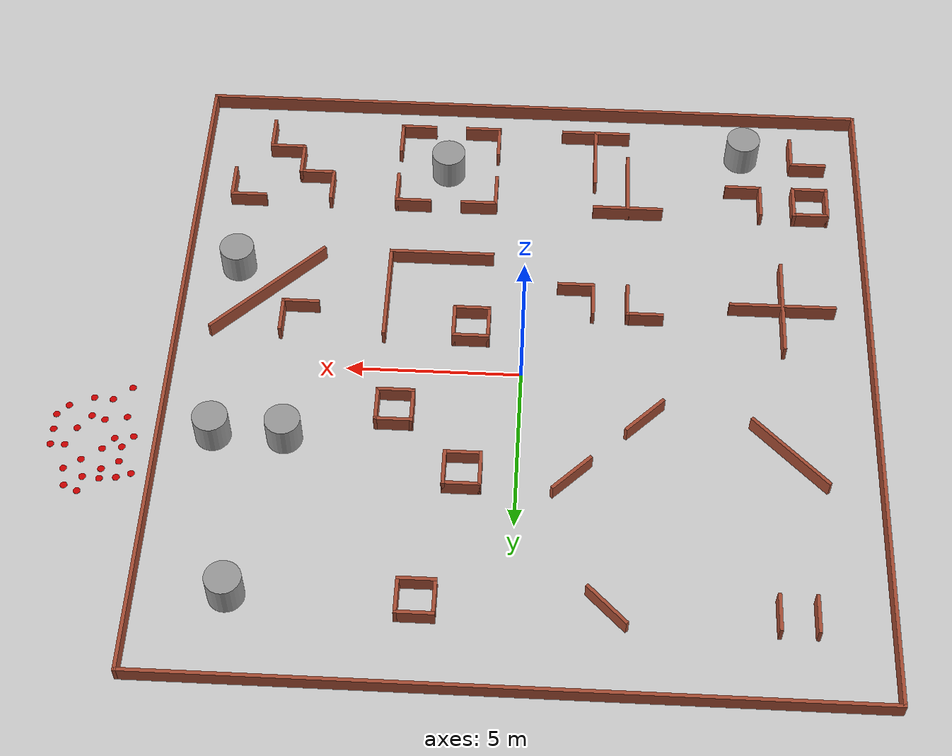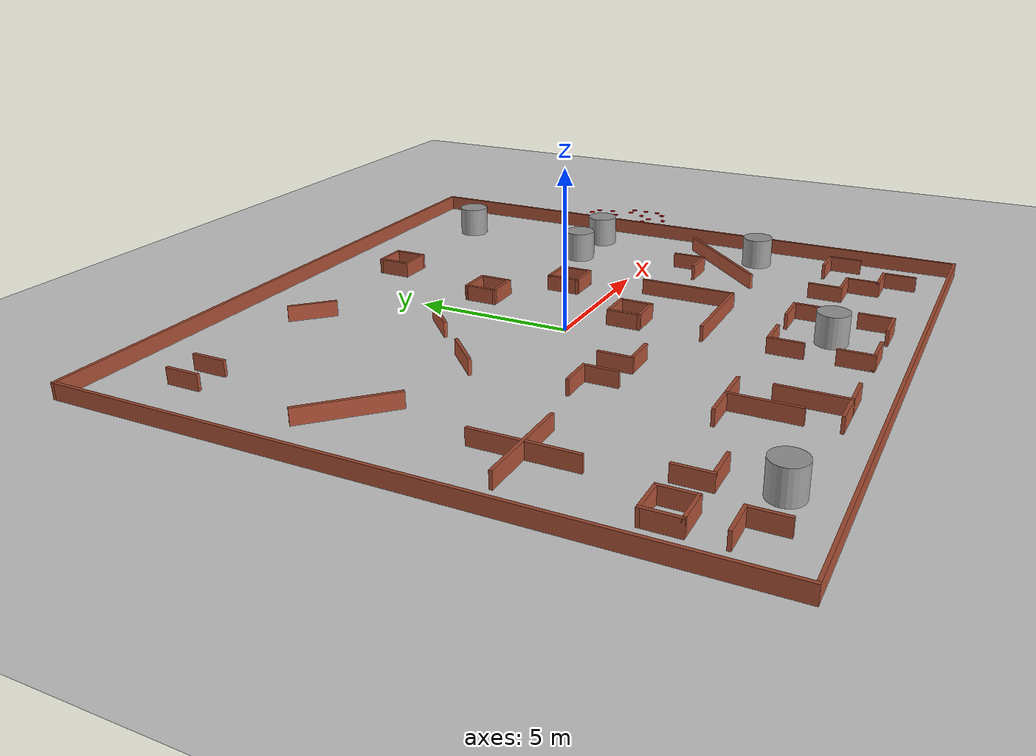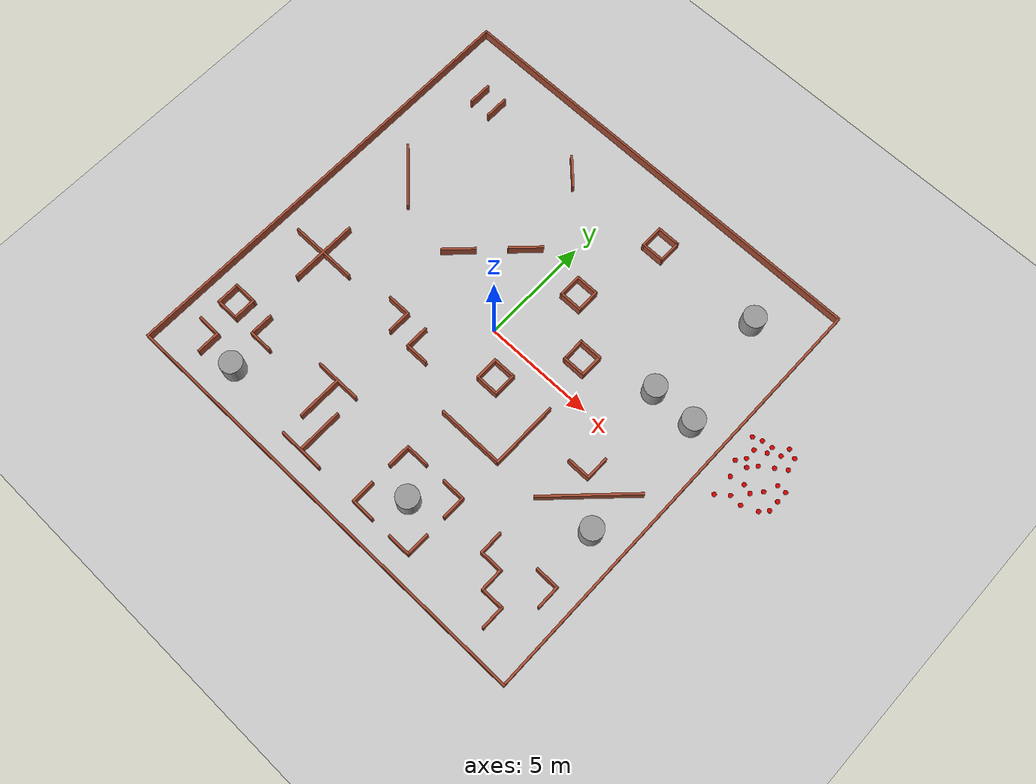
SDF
<sdf version="1.7">
 <world name="default">
  <light name="sun" type="directional">
   <pose>0 0 10 0 -0 0</pose>
   <diffuse>0.8 0.8 0.8 1</diffuse>
   <specular>0.2 0.2 0.2 1</specular>
   <attenuation>
    <range>1000</range>
    <constant>0.9</constant>
    <linear>0.01</linear>
    <quadratic>0.001</quadratic>
   </attenuation>
   <direction>-0.5 0.1 -0.9</direction>
   <spot><inner_angle>0</inner_angle><outer_angle>0</outer_angle><falloff>0</falloff></spot>
  </light>
  <model name="ground_plane">
   <static>1</static>
   <link name="link">
    <collision name="collision">
     <geometry><plane><normal>0 0 1</normal><size>100 100</size></plane></geometry>
     <surface>
      <contact><collide_bitmask>65535</collide_bitmask></contact>
      <friction><ode><mu>100</mu><mu2>50</mu2></ode></friction>
     </surface>
    </collision>
    <visual name="visual">
     <cast_shadows>0</cast_shadows>
     <geometry><plane><normal>0 0 1</normal><size>100 100</size></plane></geometry>
     <material>
      <script><uri>file://media/materials/scripts/gazebo.material</uri><name>Gazebo/Grey</name></script>
     </material>
    </visual>
   </link>
  </model>
  <gravity>0 0 -9.8</gravity>
  <magnetic_field>6e-06 2.3e-05 -4.2e-05</magnetic_field>
  <atmosphere type="adiabatic"/>
  <physics type="ode">
   <max_step_size>0.001</max_step_size>
   <real_time_factor>1</real_time_factor>
   <real_time_update_rate>1000</real_time_update_rate>
  </physics>
  <scene><ambient>0.4 0.4 0.4 1</ambient><background>0.7 0.7 0.7 1</background><shadows>1</shadows></scene>
  <spherical_coordinates>
   <surface_model>EARTH_WGS84</surface_model>
   <latitude_deg>0</latitude_deg>
   <longitude_deg>0</longitude_deg>
   <elevation>0</elevation>
   <heading_deg>0</heading_deg>
  </spherical_coordinates>
  <model name="cur_mul">
   <link name="Wall_0">
    <collision name="Wall_0_Collision">
     <geometry><box><size>20.1 0.1 0.5</size></box></geometry>
     <pose>0 0 0.25 0 -0 0</pose>
    </collision>
    <visual name="Wall_0_Visual">
     <pose>0 0 0.25 0 -0 0</pose>
     <geometry><box><size>20.1 0.1 0.5</size></box></geometry>
     <material>
      <script><uri>file://media/materials/scripts/gazebo.material</uri><name>Gazebo/Bricks</name></script>
      <ambient>0.760784 0.662745 0.627451 1</ambient>
     </material>
     <meta><layer>0</layer></meta>
    </visual>
    <pose>0 10 0 0 -0 3.14159</pose>
   </link>
   <link name="Wall_1">
    <collision name="Wall_1_Collision">
     <geometry><box><size>20.1 0.1 0.5</size></box></geometry>
     <pose>0 0 0.25 0 -0 0</pose>
    </collision>
    <visual name="Wall_1_Visual">
     <pose>0 0 0.25 0 -0 0</pose>
     <geometry><box><size>20.1 0.1 0.5</size></box></geometry>
     <material>
      <script><uri>file://media/materials/scripts/gazebo.material</uri><name>Gazebo/Bricks</name></script>
      <ambient>0.760784 0.662745 0.627451 1</ambient>
     </material>
     <meta><layer>0</layer></meta>
    </visual>
    <pose>-10 0 0 0 -0 -1.5708</pose>
   </link>
   <link name="Wall_104">
    <collision name="Wall_104_Collision">
     <geometry><box><size>1.1 0.1 0.5</size></box></geometry>
     <pose>0 0 0.25 0 -0 0</pose>
    </collision>
    <visual name="Wall_104_Visual">
     <pose>0 0 0.25 0 -0 0</pose>
     <geometry><box><size>1.1 0.1 0.5</size></box></geometry>
     <material>
      <script><uri>file://media/materials/scripts/gazebo.material</uri><name>Gazebo/Bricks</name></script>
      <ambient>0.760784 0.662745 0.627451 1</ambient>
     </material>
     <meta><layer>0</layer></meta>
    </visual>
    <pose>-9 -6.5 0 0 -0 -1.5708</pose>
   </link>
   <link name="Wall_105">
    <collision name="Wall_105_Collision">
     <geometry><box><size>1.1 0.1 0.5</size></box></geometry>
     <pose>0 0 0.25 0 -0 0</pose>
    </collision>
    <visual name="Wall_105_Visual">
     <pose>0 0 0.25 0 -0 0</pose>
     <geometry><box><size>1.1 0.1 0.5</size></box></geometry>
     <material>
      <script><uri>file://media/materials/scripts/gazebo.material</uri><name>Gazebo/Bricks</name></script>
      <ambient>0.760784 0.662745 0.627451 1</ambient>
     </material>
     <meta><layer>0</layer></meta>
    </visual>
    <pose>-8.5 -7 0 0 -0 0</pose>
   </link>
   <link name="Wall_106">
    <collision name="Wall_106_Collision">
     <geometry><box><size>1.1 0.1 0.5</size></box></geometry>
     <pose>0 0 0.25 0 -0 0</pose>
    </collision>
    <visual name="Wall_106_Visual">
     <pose>0 0 0.25 0 -0 0</pose>
     <geometry><box><size>1.1 0.1 0.5</size></box></geometry>
     <material>
      <script><uri>file://media/materials/scripts/gazebo.material</uri><name>Gazebo/Bricks</name></script>
      <ambient>0.760784 0.662745 0.627451 1</ambient>
     </material>
     <meta><layer>0</layer></meta>
    </visual>
    <pose>-8 -6.5 0 0 -0 1.5708</pose>
   </link>
   <link name="Wall_107">
    <collision name="Wall_107_Collision">
     <geometry><box><size>1.1 0.1 0.5</size></box></geometry>
     <pose>0 0 0.25 0 -0 0</pose>
    </collision>
    <visual name="Wall_107_Visual">
     <pose>0 0 0.25 0 -0 0</pose>
     <geometry><box><size>1.1 0.1 0.5</size></box></geometry>
     <material>
      <script><uri>file://media/materials/scripts/gazebo.material</uri><name>Gazebo/Bricks</name></script>
      <ambient>0.760784 0.662745 0.627451 1</ambient>
     </material>
     <meta><layer>0</layer></meta>
    </visual>
    <pose>-8.5 -6 0 0 -0 3.14159</pose>
   </link>
   <link name="Wall_109">
    <collision name="Wall_109_Collision">
     <geometry><box><size>1.1 0.1 0.5</size></box></geometry>
     <pose>0 0 0.25 0 -0 0</pose>
    </collision>
    <visual name="Wall_109_Visual">
     <pose>0 0 0.25 0 -0 0</pose>
     <geometry><box><size>1.1 0.1 0.5</size></box></geometry>
     <material>
      <script><uri>file://media/materials/scripts/gazebo.material</uri><name>Gazebo/Bricks</name></script>
      <ambient>0.760784 0.662745 0.627451 1</ambient>
     </material>
     <meta><layer>0</layer></meta>
    </visual>
    <pose>-7 -6.5 0 0 -0 -1.5708</pose>
   </link>
   <link name="Wall_110">
    <collision name="Wall_110_Collision">
     <geometry><box><size>1.1 0.1 0.5</size></box></geometry>
     <pose>0 0 0.25 0 -0 0</pose>
    </collision>
    <visual name="Wall_110_Visual">
     <pose>0 0 0.25 0 -0 0</pose>
     <geometry><box><size>1.1 0.1 0.5</size></box></geometry>
     <material>
      <script><uri>file://media/materials/scripts/gazebo.material</uri><name>Gazebo/Bricks</name></script>
      <ambient>0.760784 0.662745 0.627451 1</ambient>
     </material>
     <meta><layer>0</layer></meta>
    </visual>
    <pose>-6.5 -7 0 0 -0 0</pose>
   </link>
   <link name="Wall_112">
    <collision name="Wall_112_Collision">
     <geometry><box><size>1.1 0.1 0.5</size></box></geometry>
     <pose>0 0 0.25 0 -0 0</pose>
    </collision>
    <visual name="Wall_112_Visual">
     <pose>0 0 0.25 0 -0 0</pose>
     <geometry><box><size>1.1 0.1 0.5</size></box></geometry>
     <material>
      <script><uri>file://media/materials/scripts/gazebo.material</uri><name>Gazebo/Bricks</name></script>
      <ambient>0.760784 0.662745 0.627451 1</ambient>
     </material>
     <meta><layer>0</layer></meta>
    </visual>
    <pose>-8.5 -8 0 0 -0 0</pose>
   </link>
   <link name="Wall_113">
    <collision name="Wall_113_Collision">
     <geometry><box><size>1.1 0.1 0.5</size></box></geometry>
     <pose>0 0 0.25 0 -0 0</pose>
    </collision>
    <visual name="Wall_113_Visual">
     <pose>0 0 0.25 0 -0 0</pose>
     <geometry><box><size>1.1 0.1 0.5</size></box></geometry>
     <material>
      <script><uri>file://media/materials/scripts/gazebo.material</uri><name>Gazebo/Bricks</name></script>
      <ambient>0.760784 0.662745 0.627451 1</ambient>
     </material>
     <meta><layer>0</layer></meta>
    </visual>
    <pose>-8 -8.5 0 0 -0 -1.5708</pose>
   </link>
   <link name="Wall_115">
    <collision name="Wall_115_Collision">
     <geometry><box><size>2.1 0.1 0.5</size></box></geometry>
     <pose>0 0 0.25 0 -0 0</pose>
    </collision>
    <visual name="Wall_115_Visual">
     <pose>0 0 0.25 0 -0 0</pose>
     <geometry><box><size>2.1 0.1 0.5</size></box></geometry>
     <material>
      <script><uri>file://media/materials/scripts/gazebo.material</uri><name>Gazebo/Bricks</name></script>
      <ambient>0.760784 0.662745 0.627451 1</ambient>
     </material>
     <meta><layer>0</layer></meta>
    </visual>
    <pose>-3 -6 0 0 -0 0</pose>
   </link>
   <link name="Wall_117">
    <collision name="Wall_117_Collision">
     <geometry><box><size>2.1 0.1 0.5</size></box></geometry>
     <pose>0 0 0.25 0 -0 0</pose>
    </collision>
    <visual name="Wall_117_Visual">
     <pose>0 0 0.25 0 -0 0</pose>
     <geometry><box><size>2.1 0.1 0.5</size></box></geometry>
     <material>
      <script><uri>file://media/materials/scripts/gazebo.material</uri><name>Gazebo/Bricks</name></script>
      <ambient>0.760784 0.662745 0.627451 1</ambient>
     </material>
     <meta><layer>0</layer></meta>
    </visual>
    <pose>-3 -7 0 0 -0 -1.5708</pose>
   </link>
   <link name="Wall_119">
    <collision name="Wall_119_Collision">
     <geometry><box><size>2.1 0.1 0.5</size></box></geometry>
     <pose>0 0 0.25 0 -0 0</pose>
    </collision>
    <visual name="Wall_119_Visual">
     <pose>0 0 0.25 0 -0 0</pose>
     <geometry><box><size>2.1 0.1 0.5</size></box></geometry>
     <material>
      <script><uri>file://media/materials/scripts/gazebo.material</uri><name>Gazebo/Bricks</name></script>
      <ambient>0.760784 0.662745 0.627451 1</ambient>
     </material>
     <meta><layer>0</layer></meta>
    </visual>
    <pose>-2 -8 0 0 -0 -1.5708</pose>
   </link>
   <link name="Wall_121">
    <collision name="Wall_121_Collision">
     <geometry><box><size>2.1 0.1 0.5</size></box></geometry>
     <pose>0 0 0.25 0 -0 0</pose>
    </collision>
    <visual name="Wall_121_Visual">
     <pose>0 0 0.25 0 -0 0</pose>
     <geometry><box><size>2.1 0.1 0.5</size></box></geometry>
     <material>
      <script><uri>file://media/materials/scripts/gazebo.material</uri><name>Gazebo/Bricks</name></script>
      <ambient>0.760784 0.662745 0.627451 1</ambient>
     </material>
     <meta><layer>0</layer></meta>
    </visual>
    <pose>-2 -9 0 0 -0 0</pose>
   </link>
   <link name="Wall_128">
    <collision name="Wall_128_Collision">
     <geometry><box><size>1.1 0.1 0.5</size></box></geometry>
     <pose>0 0 0.25 0 -0 0</pose>
    </collision>
    <visual name="Wall_128_Visual">
     <pose>0 0 0.25 0 -0 0</pose>
     <geometry><box><size>1.1 0.1 0.5</size></box></geometry>
     <material>
      <script><uri>file://media/materials/scripts/gazebo.material</uri><name>Gazebo/Bricks</name></script>
      <ambient>0.760784 0.662745 0.627451 1</ambient>
     </material>
     <meta><layer>0</layer></meta>
    </visual>
    <pose>6 -6.5 0 0 -0 -1.5708</pose>
   </link>
   <link name="Wall_129">
    <collision name="Wall_129_Collision">
     <geometry><box><size>1.1 0.1 0.5</size></box></geometry>
     <pose>0 0 0.25 0 -0 0</pose>
    </collision>
    <visual name="Wall_129_Visual">
     <pose>0 0 0.25 0 -0 0</pose>
     <geometry><box><size>1.1 0.1 0.5</size></box></geometry>
     <material>
      <script><uri>file://media/materials/scripts/gazebo.material</uri><name>Gazebo/Bricks</name></script>
      <ambient>0.760784 0.662745 0.627451 1</ambient>
     </material>
     <meta><layer>0</layer></meta>
    </visual>
    <pose>6.5 -7 0 0 -0 0</pose>
   </link>
   <link name="Wall_130">
    <collision name="Wall_130_Collision">
     <geometry><box><size>1.1 0.1 0.5</size></box></geometry>
     <pose>0 0 0.25 0 -0 0</pose>
    </collision>
    <visual name="Wall_130_Visual">
     <pose>0 0 0.25 0 -0 0</pose>
     <geometry><box><size>1.1 0.1 0.5</size></box></geometry>
     <material>
      <script><uri>file://media/materials/scripts/gazebo.material</uri><name>Gazebo/Bricks</name></script>
      <ambient>0.760784 0.662745 0.627451 1</ambient>
     </material>
     <meta><layer>0</layer></meta>
    </visual>
    <pose>7 -7.5 0 0 -0 -1.5708</pose>
   </link>
   <link name="Wall_131">
    <collision name="Wall_131_Collision">
     <geometry><box><size>1.1 0.1 0.5</size></box></geometry>
     <pose>0 0 0.25 0 -0 0</pose>
    </collision>
    <visual name="Wall_131_Visual">
     <pose>0 0 0.25 0 -0 0</pose>
     <geometry><box><size>1.1 0.1 0.5</size></box></geometry>
     <material>
      <script><uri>file://media/materials/scripts/gazebo.material</uri><name>Gazebo/Bricks</name></script>
      <ambient>0.760784 0.662745 0.627451 1</ambient>
     </material>
     <meta><layer>0</layer></meta>
    </visual>
    <pose>7.5 -8 0 0 -0 0</pose>
   </link>
   <link name="Wall_132">
    <collision name="Wall_132_Collision">
     <geometry><box><size>1.1 0.1 0.5</size></box></geometry>
     <pose>0 0 0.25 0 -0 0</pose>
    </collision>
    <visual name="Wall_132_Visual">
     <pose>0 0 0.25 0 -0 0</pose>
     <geometry><box><size>1.1 0.1 0.5</size></box></geometry>
     <material>
      <script><uri>file://media/materials/scripts/gazebo.material</uri><name>Gazebo/Bricks</name></script>
      <ambient>0.760784 0.662745 0.627451 1</ambient>
     </material>
     <meta><layer>0</layer></meta>
    </visual>
    <pose>8 -8.5 0 0 -0 -1.5708</pose>
   </link>
   <link name="Wall_134">
    <collision name="Wall_134_Collision">
     <geometry><box><size>1.1 0.1 0.5</size></box></geometry>
     <pose>0 0 0.25 0 -0 0</pose>
    </collision>
    <visual name="Wall_134_Visual">
     <pose>0 0 0.25 0 -0 0</pose>
     <geometry><box><size>1.1 0.1 0.5</size></box></geometry>
     <material>
      <script><uri>file://media/materials/scripts/gazebo.material</uri><name>Gazebo/Bricks</name></script>
      <ambient>0.760784 0.662745 0.627451 1</ambient>
     </material>
     <meta><layer>0</layer></meta>
    </visual>
    <pose>8.5 -6 0 0 -0 0</pose>
   </link>
   <link name="Wall_135">
    <collision name="Wall_135_Collision">
     <geometry><box><size>1.1 0.1 0.5</size></box></geometry>
     <pose>0 0 0.25 0 -0 0</pose>
    </collision>
    <visual name="Wall_135_Visual">
     <pose>0 0 0.25 0 -0 0</pose>
     <geometry><box><size>1.1 0.1 0.5</size></box></geometry>
     <material>
      <script><uri>file://media/materials/scripts/gazebo.material</uri><name>Gazebo/Bricks</name></script>
      <ambient>0.760784 0.662745 0.627451 1</ambient>
     </material>
     <meta><layer>0</layer></meta>
    </visual>
    <pose>9 -6.5 0 0 -0 -1.5708</pose>
   </link>
   <link name="Wall_138">
    <collision name="Wall_138_Collision">
     <geometry><box><size>1.1 0.1 0.5</size></box></geometry>
     <pose>0 0 0.25 0 -0 0</pose>
    </collision>
    <visual name="Wall_138_Visual">
     <pose>0 0 0.25 0 -0 0</pose>
     <geometry><box><size>1.1 0.1 0.5</size></box></geometry>
     <material>
      <script><uri>file://media/materials/scripts/gazebo.material</uri><name>Gazebo/Bricks</name></script>
      <ambient>0.760784 0.662745 0.627451 1</ambient>
     </material>
     <meta><layer>0</layer></meta>
    </visual>
    <pose>1 -6.5 0 0 -0 1.5708</pose>
   </link>
   <link name="Wall_139">
    <collision name="Wall_139_Collision">
     <geometry><box><size>1.1 0.1 0.5</size></box></geometry>
     <pose>0 0 0.25 0 -0 0</pose>
    </collision>
    <visual name="Wall_139_Visual">
     <pose>0 0 0.25 0 -0 0</pose>
     <geometry><box><size>1.1 0.1 0.5</size></box></geometry>
     <material>
      <script><uri>file://media/materials/scripts/gazebo.material</uri><name>Gazebo/Bricks</name></script>
      <ambient>0.760784 0.662745 0.627451 1</ambient>
     </material>
     <meta><layer>0</layer></meta>
    </visual>
    <pose>1.5 -6 0 0 -0 0</pose>
   </link>
   <link name="Wall_141">
    <collision name="Wall_141_Collision">
     <geometry><box><size>1.1 0.1 0.5</size></box></geometry>
     <pose>0 0 0.25 0 -0 0</pose>
    </collision>
    <visual name="Wall_141_Visual">
     <pose>0 0 0.25 0 -0 0</pose>
     <geometry><box><size>1.1 0.1 0.5</size></box></geometry>
     <material>
      <script><uri>file://media/materials/scripts/gazebo.material</uri><name>Gazebo/Bricks</name></script>
      <ambient>0.760784 0.662745 0.627451 1</ambient>
     </material>
     <meta><layer>0</layer></meta>
    </visual>
    <pose>3.5 -6 0 0 -0 0</pose>
   </link>
   <link name="Wall_142">
    <collision name="Wall_142_Collision">
     <geometry><box><size>1.1 0.1 0.5</size></box></geometry>
     <pose>0 0 0.25 0 -0 0</pose>
    </collision>
    <visual name="Wall_142_Visual">
     <pose>0 0 0.25 0 -0 0</pose>
     <geometry><box><size>1.1 0.1 0.5</size></box></geometry>
     <material>
      <script><uri>file://media/materials/scripts/gazebo.material</uri><name>Gazebo/Bricks</name></script>
      <ambient>0.760784 0.662745 0.627451 1</ambient>
     </material>
     <meta><layer>0</layer></meta>
    </visual>
    <pose>4 -6.5 0 0 -0 -1.5708</pose>
   </link>
   <link name="Wall_144">
    <collision name="Wall_144_Collision">
     <geometry><box><size>1.1 0.1 0.5</size></box></geometry>
     <pose>0 0 0.25 0 -0 0</pose>
    </collision>
    <visual name="Wall_144_Visual">
     <pose>0 0 0.25 0 -0 0</pose>
     <geometry><box><size>1.1 0.1 0.5</size></box></geometry>
     <material>
      <script><uri>file://media/materials/scripts/gazebo.material</uri><name>Gazebo/Bricks</name></script>
      <ambient>0.760784 0.662745 0.627451 1</ambient>
     </material>
     <meta><layer>0</layer></meta>
    </visual>
    <pose>1 -8.5 0 0 -0 -1.5708</pose>
   </link>
   <link name="Wall_145">
    <collision name="Wall_145_Collision">
     <geometry><box><size>1.1 0.1 0.5</size></box></geometry>
     <pose>0 0 0.25 0 -0 0</pose>
    </collision>
    <visual name="Wall_145_Visual">
     <pose>0 0 0.25 0 -0 0</pose>
     <geometry><box><size>1.1 0.1 0.5</size></box></geometry>
     <material>
      <script><uri>file://media/materials/scripts/gazebo.material</uri><name>Gazebo/Bricks</name></script>
      <ambient>0.760784 0.662745 0.627451 1</ambient>
     </material>
     <meta><layer>0</layer></meta>
    </visual>
    <pose>1.5 -9 0 0 -0 0</pose>
   </link>
   <link name="Wall_147">
    <collision name="Wall_147_Collision">
     <geometry><box><size>1.1 0.1 0.5</size></box></geometry>
     <pose>0 0 0.25 0 -0 0</pose>
    </collision>
    <visual name="Wall_147_Visual">
     <pose>0 0 0.25 0 -0 0</pose>
     <geometry><box><size>1.1 0.1 0.5</size></box></geometry>
     <material>
      <script><uri>file://media/materials/scripts/gazebo.material</uri><name>Gazebo/Bricks</name></script>
      <ambient>0.760784 0.662745 0.627451 1</ambient>
     </material>
     <meta><layer>0</layer></meta>
    </visual>
    <pose>4 -8.5 0 0 -0 -1.5708</pose>
   </link>
   <link name="Wall_148">
    <collision name="Wall_148_Collision">
     <geometry><box><size>1.1 0.1 0.5</size></box></geometry>
     <pose>0 0 0.25 0 -0 0</pose>
    </collision>
    <visual name="Wall_148_Visual">
     <pose>0 0 0.25 0 -0 0</pose>
     <geometry><box><size>1.1 0.1 0.5</size></box></geometry>
     <material>
      <script><uri>file://media/materials/scripts/gazebo.material</uri><name>Gazebo/Bricks</name></script>
      <ambient>0.760784 0.662745 0.627451 1</ambient>
     </material>
     <meta><layer>0</layer></meta>
    </visual>
    <pose>3.5 -9 0 0 -0 3.14159</pose>
   </link>
   <link name="Wall_151">
    <collision name="Wall_151_Collision">
     <geometry><box><size>4.34264 0.1 0.5</size></box></geometry>
     <pose>0 0 0.25 0 -0 0</pose>
    </collision>
    <visual name="Wall_151_Visual">
     <pose>0 0 0.25 0 -0 0</pose>
     <geometry><box><size>4.34264 0.1 0.5</size></box></geometry>
     <material>
      <script><uri>file://media/materials/scripts/gazebo.material</uri><name>Gazebo/Bricks</name></script>
      <ambient>0.760784 0.662745 0.627451 1</ambient>
     </material>
     <meta><layer>0</layer></meta>
    </visual>
    <pose>7.5 -2.5 0 0 -0 0.785398</pose>
   </link>
   <link name="Wall_153">
    <collision name="Wall_153_Collision">
     <geometry><box><size>1.1 0.1 0.5</size></box></geometry>
     <pose>0 0 0.25 0 -0 0</pose>
    </collision>
    <visual name="Wall_153_Visual">
     <pose>0 0 0.25 0 -0 0</pose>
     <geometry><box><size>1.1 0.1 0.5</size></box></geometry>
     <material>
      <script><uri>file://media/materials/scripts/gazebo.material</uri><name>Gazebo/Bricks</name></script>
      <ambient>0.760784 0.662745 0.627451 1</ambient>
     </material>
     <meta><layer>0</layer></meta>
    </visual>
    <pose>7 -1.5 0 0 -0 -1.5708</pose>
   </link>
   <link name="Wall_154">
    <collision name="Wall_154_Collision">
     <geometry><box><size>1.1 0.1 0.5</size></box></geometry>
     <pose>0 0 0.25 0 -0 0</pose>
    </collision>
    <visual name="Wall_154_Visual">
     <pose>0 0 0.25 0 -0 0</pose>
     <geometry><box><size>1.1 0.1 0.5</size></box></geometry>
     <material>
      <script><uri>file://media/materials/scripts/gazebo.material</uri><name>Gazebo/Bricks</name></script>
      <ambient>0.760784 0.662745 0.627451 1</ambient>
     </material>
     <meta><layer>0</layer></meta>
    </visual>
    <pose>6.5 -2 0 0 -0 3.14159</pose>
   </link>
   <link name="Wall_156">
    <collision name="Wall_156_Collision">
     <geometry><box><size>3.1 0.1 0.5</size></box></geometry>
     <pose>0 0 0.25 0 -0 0</pose>
    </collision>
    <visual name="Wall_156_Visual">
     <pose>0 0 0.25 0 -0 0</pose>
     <geometry><box><size>3.1 0.1 0.5</size></box></geometry>
     <material>
      <script><uri>file://media/materials/scripts/gazebo.material</uri><name>Gazebo/Bricks</name></script>
      <ambient>0.760784 0.662745 0.627451 1</ambient>
     </material>
     <meta><layer>0</layer></meta>
    </visual>
    <pose>2.5 -4 0 0 -0 0</pose>
   </link>
   <link name="Wall_157">
    <collision name="Wall_157_Collision">
     <geometry><box><size>3.1 0.1 0.5</size></box></geometry>
     <pose>0 0 0.25 0 -0 0</pose>
    </collision>
    <visual name="Wall_157_Visual">
     <pose>0 0 0.25 0 -0 0</pose>
     <geometry><box><size>3.1 0.1 0.5</size></box></geometry>
     <material>
      <script><uri>file://media/materials/scripts/gazebo.material</uri><name>Gazebo/Bricks</name></script>
      <ambient>0.760784 0.662745 0.627451 1</ambient>
     </material>
     <meta><layer>0</layer></meta>
    </visual>
    <pose>4 -2.5 0 0 -0 1.5708</pose>
   </link>
   <link name="Wall_2">
    <collision name="Wall_2_Collision">
     <geometry><box><size>20.1 0.1 0.5</size></box></geometry>
     <pose>0 0 0.25 0 -0 0</pose>
    </collision>
    <visual name="Wall_2_Visual">
     <pose>0 0 0.25 0 -0 0</pose>
     <geometry><box><size>20.1 0.1 0.5</size></box></geometry>
     <material>
      <script><uri>file://media/materials/scripts/gazebo.material</uri><name>Gazebo/Bricks</name></script>
      <ambient>0.760784 0.662745 0.627451 1</ambient>
     </material>
     <meta><layer>0</layer></meta>
    </visual>
    <pose>0 -10 0 0 -0 0</pose>
   </link>
   <link name="Wall_3">
    <collision name="Wall_3_Collision">
     <geometry><box><size>20.1 0.1 0.5</size></box></geometry>
     <pose>0 0 0.25 0 -0 0</pose>
    </collision>
    <visual name="Wall_3_Visual">
     <pose>0 0 0.25 0 -0 0</pose>
     <geometry><box><size>20.1 0.1 0.5</size></box></geometry>
     <material>
      <script><uri>file://media/materials/scripts/gazebo.material</uri><name>Gazebo/Bricks</name></script>
      <ambient>0.760784 0.662745 0.627451 1</ambient>
     </material>
     <meta><layer>0</layer></meta>
    </visual>
    <pose>10 0 0 0 -0 1.5708</pose>
   </link>
   <link name="Wall_45">
    <collision name="Wall_45_Collision">
     <geometry><box><size>1.1 0.1 0.5</size></box></geometry>
     <pose>0 0 0.25 0 -0 0</pose>
    </collision>
    <visual name="Wall_45_Visual">
     <pose>0 0 0.25 0 -0 0</pose>
     <geometry><box><size>1.1 0.1 0.5</size></box></geometry>
     <material>
      <script><uri>file://media/materials/scripts/gazebo.material</uri><name>Gazebo/Bricks</name></script>
      <ambient>0.760784 0.662745 0.627451 1</ambient>
     </material>
     <meta><layer>0</layer></meta>
    </visual>
    <pose>-8 7.5 0 0 -0 -1.5708</pose>
   </link>
   <link name="Wall_47">
    <collision name="Wall_47_Collision">
     <geometry><box><size>1.1 0.1 0.5</size></box></geometry>
     <pose>0 0 0.25 0 -0 0</pose>
    </collision>
    <visual name="Wall_47_Visual">
     <pose>0 0 0.25 0 -0 0</pose>
     <geometry><box><size>1.1 0.1 0.5</size></box></geometry>
     <material>
      <script><uri>file://media/materials/scripts/gazebo.material</uri><name>Gazebo/Bricks</name></script>
      <ambient>0.760784 0.662745 0.627451 1</ambient>
     </material>
     <meta><layer>0</layer></meta>
    </visual>
    <pose>-7 7.5 0 0 -0 -1.5708</pose>
   </link>
   <link name="Wall_49">
    <collision name="Wall_49_Collision">
     <geometry><box><size>1.51421 0.1 0.5</size></box></geometry>
     <pose>0 0 0.25 0 -0 0</pose>
    </collision>
    <visual name="Wall_49_Visual">
     <pose>0 0 0.25 0 -0 0</pose>
     <geometry><box><size>1.51421 0.1 0.5</size></box></geometry>
     <material>
      <script><uri>file://media/materials/scripts/gazebo.material</uri><name>Gazebo/Bricks</name></script>
      <ambient>0.760784 0.662745 0.627451 1</ambient>
     </material>
     <meta><layer>0</layer></meta>
    </visual>
    <pose>-2.5 7.5 0 0 -0 -0.785398</pose>
   </link>
   <link name="Wall_51">
    <collision name="Wall_51_Collision">
     <geometry><box><size>1.1 0.1 0.5</size></box></geometry>
     <pose>0 0 0.25 0 -0 0</pose>
    </collision>
    <visual name="Wall_51_Visual">
     <pose>0 0 0.25 0 -0 0</pose>
     <geometry><box><size>1.1 0.1 0.5</size></box></geometry>
     <material>
      <script><uri>file://media/materials/scripts/gazebo.material</uri><name>Gazebo/Bricks</name></script>
      <ambient>0.760784 0.662745 0.627451 1</ambient>
     </material>
     <meta><layer>0</layer></meta>
    </visual>
    <pose>2.5 7 0 0 -0 0</pose>
   </link>
   <link name="Wall_52">
    <collision name="Wall_52_Collision">
     <geometry><box><size>1.1 0.1 0.5</size></box></geometry>
     <pose>0 0 0.25 0 -0 0</pose>
    </collision>
    <visual name="Wall_52_Visual">
     <pose>0 0 0.25 0 -0 0</pose>
     <geometry><box><size>1.1 0.1 0.5</size></box></geometry>
     <material>
      <script><uri>file://media/materials/scripts/gazebo.material</uri><name>Gazebo/Bricks</name></script>
      <ambient>0.760784 0.662745 0.627451 1</ambient>
     </material>
     <meta><layer>0</layer></meta>
    </visual>
    <pose>3 7.5 0 0 -0 1.5708</pose>
   </link>
   <link name="Wall_53">
    <collision name="Wall_53_Collision">
     <geometry><box><size>1.1 0.1 0.5</size></box></geometry>
     <pose>0 0 0.25 0 -0 0</pose>
    </collision>
    <visual name="Wall_53_Visual">
     <pose>0 0 0.25 0 -0 0</pose>
     <geometry><box><size>1.1 0.1 0.5</size></box></geometry>
     <material>
      <script><uri>file://media/materials/scripts/gazebo.material</uri><name>Gazebo/Bricks</name></script>
      <ambient>0.760784 0.662745 0.627451 1</ambient>
     </material>
     <meta><layer>0</layer></meta>
    </visual>
    <pose>2.5 8 0 0 -0 3.14159</pose>
   </link>
   <link name="Wall_54">
    <collision name="Wall_54_Collision">
     <geometry><box><size>1.1 0.1 0.5</size></box></geometry>
     <pose>0 0 0.25 0 -0 0</pose>
    </collision>
    <visual name="Wall_54_Visual">
     <pose>0 0 0.25 0 -0 0</pose>
     <geometry><box><size>1.1 0.1 0.5</size></box></geometry>
     <material>
      <script><uri>file://media/materials/scripts/gazebo.material</uri><name>Gazebo/Bricks</name></script>
      <ambient>0.760784 0.662745 0.627451 1</ambient>
     </material>
     <meta><layer>0</layer></meta>
    </visual>
    <pose>2 7.5 0 0 -0 -1.5708</pose>
   </link>
   <link name="Wall_56">
    <collision name="Wall_56_Collision">
     <geometry><box><size>2.92843 0.1 0.5</size></box></geometry>
     <pose>0 0 0.25 0 -0 0</pose>
    </collision>
    <visual name="Wall_56_Visual">
     <pose>0 0 0.25 0 -0 0</pose>
     <geometry><box><size>2.92843 0.1 0.5</size></box></geometry>
     <material>
      <script><uri>file://media/materials/scripts/gazebo.material</uri><name>Gazebo/Bricks</name></script>
      <ambient>0.760784 0.662745 0.627451 1</ambient>
     </material>
     <meta><layer>0</layer></meta>
    </visual>
    <pose>-7.5 2.5 0 0 -0 -0.785398</pose>
   </link>
   <link name="Wall_58">
    <collision name="Wall_58_Collision">
     <geometry><box><size>1.51421 0.1 0.5</size></box></geometry>
     <pose>0 0 0.25 0 -0 0</pose>
    </collision>
    <visual name="Wall_58_Visual">
     <pose>0 0 0.25 0 -0 0</pose>
     <geometry><box><size>1.51421 0.1 0.5</size></box></geometry>
     <material>
      <script><uri>file://media/materials/scripts/gazebo.material</uri><name>Gazebo/Bricks</name></script>
      <ambient>0.760784 0.662745 0.627451 1</ambient>
     </material>
     <meta><layer>0</layer></meta>
    </visual>
    <pose>-1.5 3.5 0 0 -0 0.785398</pose>
   </link>
   <link name="Wall_60">
    <collision name="Wall_60_Collision">
     <geometry><box><size>1.51421 0.1 0.5</size></box></geometry>
     <pose>0 0 0.25 0 -0 0</pose>
    </collision>
    <visual name="Wall_60_Visual">
     <pose>0 0 0.25 0 -0 0</pose>
     <geometry><box><size>1.51421 0.1 0.5</size></box></geometry>
     <material>
      <script><uri>file://media/materials/scripts/gazebo.material</uri><name>Gazebo/Bricks</name></script>
      <ambient>0.760784 0.662745 0.627451 1</ambient>
     </material>
     <meta><layer>0</layer></meta>
    </visual>
    <pose>-3.5 1.5 0 0 -0 0.785398</pose>
   </link>
   <link name="Wall_62">
    <collision name="Wall_62_Collision">
     <geometry><box><size>1.1 0.1 0.5</size></box></geometry>
     <pose>0 0 0.25 0 -0 0</pose>
    </collision>
    <visual name="Wall_62_Visual">
     <pose>0 0 0.25 0 -0 0</pose>
     <geometry><box><size>1.1 0.1 0.5</size></box></geometry>
     <material>
      <script><uri>file://media/materials/scripts/gazebo.material</uri><name>Gazebo/Bricks</name></script>
      <ambient>0.760784 0.662745 0.627451 1</ambient>
     </material>
     <meta><layer>0</layer></meta>
    </visual>
    <pose>2 3.5 0 0 -0 -1.5708</pose>
   </link>
   <link name="Wall_63">
    <collision name="Wall_63_Collision">
     <geometry><box><size>1.1 0.1 0.5</size></box></geometry>
     <pose>0 0 0.25 0 -0 0</pose>
    </collision>
    <visual name="Wall_63_Visual">
     <pose>0 0 0.25 0 -0 0</pose>
     <geometry><box><size>1.1 0.1 0.5</size></box></geometry>
     <material>
      <script><uri>file://media/materials/scripts/gazebo.material</uri><name>Gazebo/Bricks</name></script>
      <ambient>0.760784 0.662745 0.627451 1</ambient>
     </material>
     <meta><layer>0</layer></meta>
    </visual>
    <pose>1.5 3 0 0 -0 3.14159</pose>
   </link>
   <link name="Wall_64">
    <collision name="Wall_64_Collision">
     <geometry><box><size>1.1 0.1 0.5</size></box></geometry>
     <pose>0 0 0.25 0 -0 0</pose>
    </collision>
    <visual name="Wall_64_Visual">
     <pose>0 0 0.25 0 -0 0</pose>
     <geometry><box><size>1.1 0.1 0.5</size></box></geometry>
     <material>
      <script><uri>file://media/materials/scripts/gazebo.material</uri><name>Gazebo/Bricks</name></script>
      <ambient>0.760784 0.662745 0.627451 1</ambient>
     </material>
     <meta><layer>0</layer></meta>
    </visual>
    <pose>1 3.5 0 0 -0 1.5708</pose>
   </link>
   <link name="Wall_65">
    <collision name="Wall_65_Collision">
     <geometry><box><size>1.1 0.1 0.5</size></box></geometry>
     <pose>0 0 0.25 0 -0 0</pose>
    </collision>
    <visual name="Wall_65_Visual">
     <pose>0 0 0.25 0 -0 0</pose>
     <geometry><box><size>1.1 0.1 0.5</size></box></geometry>
     <material>
      <script><uri>file://media/materials/scripts/gazebo.material</uri><name>Gazebo/Bricks</name></script>
      <ambient>0.760784 0.662745 0.627451 1</ambient>
     </material>
     <meta><layer>0</layer></meta>
    </visual>
    <pose>1.5 4 0 0 -0 0</pose>
   </link>
   <link name="Wall_67">
    <collision name="Wall_67_Collision">
     <geometry><box><size>1.1 0.1 0.5</size></box></geometry>
     <pose>0 0 0.25 0 -0 0</pose>
    </collision>
    <visual name="Wall_67_Visual">
     <pose>0 0 0.25 0 -0 0</pose>
     <geometry><box><size>1.1 0.1 0.5</size></box></geometry>
     <material>
      <script><uri>file://media/materials/scripts/gazebo.material</uri><name>Gazebo/Bricks</name></script>
      <ambient>0.760784 0.662745 0.627451 1</ambient>
     </material>
     <meta><layer>0</layer></meta>
    </visual>
    <pose>4 1.5 0 0 -0 -1.5708</pose>
   </link>
   <link name="Wall_68">
    <collision name="Wall_68_Collision">
     <geometry><box><size>1.1 0.1 0.5</size></box></geometry>
     <pose>0 0 0.25 0 -0 0</pose>
    </collision>
    <visual name="Wall_68_Visual">
     <pose>0 0 0.25 0 -0 0</pose>
     <geometry><box><size>1.1 0.1 0.5</size></box></geometry>
     <material>
      <script><uri>file://media/materials/scripts/gazebo.material</uri><name>Gazebo/Bricks</name></script>
      <ambient>0.760784 0.662745 0.627451 1</ambient>
     </material>
     <meta><layer>0</layer></meta>
    </visual>
    <pose>3.5 1 0 0 -0 3.14159</pose>
   </link>
   <link name="Wall_69">
    <collision name="Wall_69_Collision">
     <geometry><box><size>1.1 0.1 0.5</size></box></geometry>
     <pose>0 0 0.25 0 -0 0</pose>
    </collision>
    <visual name="Wall_69_Visual">
     <pose>0 0 0.25 0 -0 0</pose>
     <geometry><box><size>1.1 0.1 0.5</size></box></geometry>
     <material>
      <script><uri>file://media/materials/scripts/gazebo.material</uri><name>Gazebo/Bricks</name></script>
      <ambient>0.760784 0.662745 0.627451 1</ambient>
     </material>
     <meta><layer>0</layer></meta>
    </visual>
    <pose>3 1.5 0 0 -0 1.5708</pose>
   </link>
   <link name="Wall_70">
    <collision name="Wall_70_Collision">
     <geometry><box><size>1.1 0.1 0.5</size></box></geometry>
     <pose>0 0 0.25 0 -0 0</pose>
    </collision>
    <visual name="Wall_70_Visual">
     <pose>0 0 0.25 0 -0 0</pose>
     <geometry><box><size>1.1 0.1 0.5</size></box></geometry>
     <material>
      <script><uri>file://media/materials/scripts/gazebo.material</uri><name>Gazebo/Bricks</name></script>
      <ambient>0.760784 0.662745 0.627451 1</ambient>
     </material>
     <meta><layer>0</layer></meta>
    </visual>
    <pose>3.5 2 0 0 -0 0</pose>
   </link>
   <link name="Wall_72">
    <collision name="Wall_72_Collision">
     <geometry><box><size>3.1 0.1 0.5</size></box></geometry>
     <pose>0 0 0.25 0 -0 0</pose>
    </collision>
    <visual name="Wall_72_Visual">
     <pose>0 0 0.25 0 -0 0</pose>
     <geometry><box><size>3.1 0.1 0.5</size></box></geometry>
     <material>
      <script><uri>file://media/materials/scripts/gazebo.material</uri><name>Gazebo/Bricks</name></script>
      <ambient>0.760784 0.662745 0.627451 1</ambient>
     </material>
     <meta><layer>0</layer></meta>
    </visual>
    <pose>-7.5 -2.5 0 0 -0 0</pose>
   </link>
   <link name="Wall_74">
    <collision name="Wall_74_Collision">
     <geometry><box><size>3.1 0.1 0.5</size></box></geometry>
     <pose>0 0 0.25 0 -0 0</pose>
    </collision>
    <visual name="Wall_74_Visual">
     <pose>0 0 0.25 0 -0 0</pose>
     <geometry><box><size>3.1 0.1 0.5</size></box></geometry>
     <material>
      <script><uri>file://media/materials/scripts/gazebo.material</uri><name>Gazebo/Bricks</name></script>
      <ambient>0.760784 0.662745 0.627451 1</ambient>
     </material>
     <meta><layer>0</layer></meta>
    </visual>
    <pose>-7.5 -2.5 0 0 -0 -1.5708</pose>
   </link>
   <link name="Wall_76">
    <collision name="Wall_76_Collision">
     <geometry><box><size>1.1 0.1 0.5</size></box></geometry>
     <pose>0 0 0.25 0 -0 0</pose>
    </collision>
    <visual name="Wall_76_Visual">
     <pose>0 0 0.25 0 -0 0</pose>
     <geometry><box><size>1.1 0.1 0.5</size></box></geometry>
     <material>
      <script><uri>file://media/materials/scripts/gazebo.material</uri><name>Gazebo/Bricks</name></script>
      <ambient>0.760784 0.662745 0.627451 1</ambient>
     </material>
     <meta><layer>0</layer></meta>
    </visual>
    <pose>-3.5 -2 0 0 -0 0</pose>
   </link>
   <link name="Wall_77">
    <collision name="Wall_77_Collision">
     <geometry><box><size>1.1 0.1 0.5</size></box></geometry>
     <pose>0 0 0.25 0 -0 0</pose>
    </collision>
    <visual name="Wall_77_Visual">
     <pose>0 0 0.25 0 -0 0</pose>
     <geometry><box><size>1.1 0.1 0.5</size></box></geometry>
     <material>
      <script><uri>file://media/materials/scripts/gazebo.material</uri><name>Gazebo/Bricks</name></script>
      <ambient>0.760784 0.662745 0.627451 1</ambient>
     </material>
     <meta><layer>0</layer></meta>
    </visual>
    <pose>-3 -2.5 0 0 -0 -1.5708</pose>
   </link>
   <link name="Wall_79">
    <collision name="Wall_79_Collision">
     <geometry><box><size>1.1 0.1 0.5</size></box></geometry>
     <pose>0 0 0.25 0 -0 0</pose>
    </collision>
    <visual name="Wall_79_Visual">
     <pose>0 0 0.25 0 -0 0</pose>
     <geometry><box><size>1.1 0.1 0.5</size></box></geometry>
     <material>
      <script><uri>file://media/materials/scripts/gazebo.material</uri><name>Gazebo/Bricks</name></script>
      <ambient>0.760784 0.662745 0.627451 1</ambient>
     </material>
     <meta><layer>0</layer></meta>
    </visual>
    <pose>-2 -2.5 0 0 -0 -1.5708</pose>
   </link>
   <link name="Wall_80">
    <collision name="Wall_80_Collision">
     <geometry><box><size>1.1 0.1 0.5</size></box></geometry>
     <pose>0 0 0.25 0 -0 0</pose>
    </collision>
    <visual name="Wall_80_Visual">
     <pose>0 0 0.25 0 -0 0</pose>
     <geometry><box><size>1.1 0.1 0.5</size></box></geometry>
     <material>
      <script><uri>file://media/materials/scripts/gazebo.material</uri><name>Gazebo/Bricks</name></script>
      <ambient>0.760784 0.662745 0.627451 1</ambient>
     </material>
     <meta><layer>0</layer></meta>
    </visual>
    <pose>-1.5 -3 0 0 -0 0</pose>
   </link>
   <link name="Wall_82">
    <collision name="Wall_82_Collision">
     <geometry><box><size>1.1 0.1 0.5</size></box></geometry>
     <pose>0 0 0.25 0 -0 0</pose>
    </collision>
    <visual name="Wall_82_Visual">
     <pose>0 0 0.25 0 -0 0</pose>
     <geometry><box><size>1.1 0.1 0.5</size></box></geometry>
     <material>
      <script><uri>file://media/materials/scripts/gazebo.material</uri><name>Gazebo/Bricks</name></script>
      <ambient>0.760784 0.662745 0.627451 1</ambient>
     </material>
     <meta><layer>0</layer></meta>
    </visual>
    <pose>2 -1.5 0 0 -0 -1.5708</pose>
   </link>
   <link name="Wall_83">
    <collision name="Wall_83_Collision">
     <geometry><box><size>1.1 0.1 0.5</size></box></geometry>
     <pose>0 0 0.25 0 -0 0</pose>
    </collision>
    <visual name="Wall_83_Visual">
     <pose>0 0 0.25 0 -0 0</pose>
     <geometry><box><size>1.1 0.1 0.5</size></box></geometry>
     <material>
      <script><uri>file://media/materials/scripts/gazebo.material</uri><name>Gazebo/Bricks</name></script>
      <ambient>0.760784 0.662745 0.627451 1</ambient>
     </material>
     <meta><layer>0</layer></meta>
    </visual>
    <pose>1.5 -2 0 0 -0 3.14159</pose>
   </link>
   <link name="Wall_84">
    <collision name="Wall_84_Collision">
     <geometry><box><size>1.1 0.1 0.5</size></box></geometry>
     <pose>0 0 0.25 0 -0 0</pose>
    </collision>
    <visual name="Wall_84_Visual">
     <pose>0 0 0.25 0 -0 0</pose>
     <geometry><box><size>1.1 0.1 0.5</size></box></geometry>
     <material>
      <script><uri>file://media/materials/scripts/gazebo.material</uri><name>Gazebo/Bricks</name></script>
      <ambient>0.760784 0.662745 0.627451 1</ambient>
     </material>
     <meta><layer>0</layer></meta>
    </visual>
    <pose>1 -1.5 0 0 -0 1.5708</pose>
   </link>
   <link name="Wall_85">
    <collision name="Wall_85_Collision">
     <geometry><box><size>1.1 0.1 0.5</size></box></geometry>
     <pose>0 0 0.25 0 -0 0</pose>
    </collision>
    <visual name="Wall_85_Visual">
     <pose>0 0 0.25 0 -0 0</pose>
     <geometry><box><size>1.1 0.1 0.5</size></box></geometry>
     <material>
      <script><uri>file://media/materials/scripts/gazebo.material</uri><name>Gazebo/Bricks</name></script>
      <ambient>0.760784 0.662745 0.627451 1</ambient>
     </material>
     <meta><layer>0</layer></meta>
    </visual>
    <pose>1.5 -1 0 0 -0 0</pose>
   </link>
   <static>1</static>
  </model>
  <model name="unit_cylinder">
   <pose>7.5 7.5 0.499998 3e-06 -2e-06 0</pose>
   <link name="link">
    <inertial>
     <mass>1</mass>
     <inertia><ixx>0.145833</ixx><ixy>0</ixy><ixz>0</ixz><iyy>0.145833</iyy><iyz>0</iyz><izz>0.125</izz></inertia>
    </inertial>
    <collision name="collision">
     <geometry><cylinder><radius>0.5</radius><length>1</length></cylinder></geometry>
    </collision>
    <visual name="visual">
     <geometry><cylinder><radius>0.5</radius><length>1</length></cylinder></geometry>
     <material>
      <script><name>Gazebo/Grey</name><uri>file://media/materials/scripts/gazebo.material</uri></script>
     </material>
    </visual>
   </link>
  </model>
  <model name="unit_cylinder_2">
   <pose>2.5 -7.5 0.499994 -3e-06 -2e-06 0</pose>
   <link name="link">
    <inertial>
     <mass>1</mass>
     <inertia><ixx>0.145833</ixx><ixy>0</ixy><ixz>0</ixz><iyy>0.145833</iyy><iyz>0</iyz><izz>0.125</izz></inertia>
    </inertial>
    <collision name="collision">
     <geometry><cylinder><radius>0.5</radius><length>1</length></cylinder></geometry>
    </collision>
    <visual name="visual">
     <geometry><cylinder><radius>0.5</radius><length>1</length></cylinder></geometry>
     <material>
      <script><name>Gazebo/Grey</name><uri>file://media/materials/scripts/gazebo.material</uri></script>
     </material>
    </visual>
   </link>
  </model>
  <model name="unit_cylinder_3">
   <pose>8.5 -3.5 0.499998 3e-06 4e-06 -0</pose>
   <link name="link">
    <inertial>
     <mass>1</mass>
     <inertia><ixx>0.145833</ixx><ixy>0</ixy><ixz>0</ixz><iyy>0.145833</iyy><iyz>0</iyz><izz>0.125</izz></inertia>
    </inertial>
    <collision name="collision">
     <geometry><cylinder><radius>0.5</radius><length>1</length></cylinder></geometry>
    </collision>
    <visual name="visual">
     <geometry><cylinder><radius>0.5</radius><length>1</length></cylinder></geometry>
     <material>
      <script><name>Gazebo/Grey</name><uri>file://media/materials/scripts/gazebo.material</uri></script>
     </material>
    </visual>
   </link>
  </model>
  <model name="unit_cylinder_4">
   <pose>-6.5 -8.5 0.499994 -4e-06 -3e-06 -0</pose>
   <link name="link">
    <inertial>
     <mass>1</mass>
     <inertia><ixx>0.145833</ixx><ixy>0</ixy><ixz>0</ixz><iyy>0.145833</iyy><iyz>0</iyz><izz>0.125</izz></inertia>
    </inertial>
    <collision name="collision">
     <geometry><cylinder><radius>0.5</radius><length>1</length></cylinder></geometry>
    </collision>
    <visual name="visual">
     <geometry><cylinder><radius>0.5</radius><length>1</length></cylinder></geometry>
     <material>
      <script><name>Gazebo/Grey</name><uri>file://media/materials/scripts/gazebo.material</uri></script>
     </material>
    </visual>
   </link>
  </model>
  <model name="unit_cylinder_0">
   <pose>6.5 2.5 0.499994 -3e-06 -1e-06 -0</pose>
   <link name="link">
    <inertial>
     <mass>1</mass>
     <inertia><ixx>0.145833</ixx><ixy>0</ixy><ixz>0</ixz><iyy>0.145833</iyy><iyz>0</iyz><izz>0.125</izz></inertia>
    </inertial>
    <collision name="collision">
     <geometry><cylinder><radius>0.5</radius><length>1</length></cylinder></geometry>
    </collision>
    <visual name="visual">
     <geometry><cylinder><radius>0.5</radius><length>1</length></cylinder></geometry>
     <material>
      <script><name>Gazebo/Grey</name><uri>file://media/materials/scripts/gazebo.material</uri></script>
     </material>
    </visual>
   </link>
  </model>
  <model name="unit_cylinder_1">
   <pose>8.5 2.5 0.499994 -3e-06 -1e-06 -0</pose>
   <link name="link">
    <inertial>
     <mass>1</mass>
     <inertia><ixx>0.145833</ixx><ixy>0</ixy><ixz>0</ixz><iyy>0.145833</iyy><iyz>0</iyz><izz>0.125</izz></inertia>
    </inertial>
    <collision name="collision">
     <geometry><cylinder><radius>0.5</radius><length>1</length></cylinder></geometry>
    </collision>
    <visual name="visual">
     <geometry><cylinder><radius>0.5</radius><length>1</length></cylinder></geometry>
     <material>
      <script><name>Gazebo/Grey</name><uri>file://media/materials/scripts/gazebo.material</uri></script>
     </material>
    </visual>
   </link>
  </model>
  <model name="target_red">
   <link name="link">
    <inertial>
     <mass>1</mass>
     <inertia><ixx>0.145833</ixx><ixy>0</ixy><ixz>0</ixz><iyy>0.145833</iyy><iyz>0</iyz><izz>0.125</izz></inertia>
    </inertial>
    <visual name="visual">
     <geometry><cylinder><radius>0.1</radius><length>0.01</length></cylinder></geometry>
     <material>
      <script><name>Gazebo/Grey</name><uri>file://media/materials/scripts/gazebo.material</uri></script>
      <shader type="pixel"><normal_map>__default__</normal_map></shader>
      <ambient>0.8 0 0 1</ambient>
      <diffuse>0.8 0 0 1</diffuse>
      <specular>0.8 0 0 1</specular>
      <emissive>0 0 0 1</emissive>
     </material>
    </visual>
    <collision name="collision">
     <geometry><cylinder><radius>0.1</radius><length>0.01</length></cylinder></geometry>
     <surface>
      <friction>
       <ode><mu>1</mu><mu2>1</mu2><fdir1>0 0 0</fdir1><slip1>0</slip1><slip2>0</slip2></ode>
       <torsional>
        <coefficient>1</coefficient>
        <patch_radius>0</patch_radius>
        <surface_radius>0</surface_radius>
        <use_patch_radius>1</use_patch_radius>
        <ode><slip>0</slip></ode>
       </torsional>
      </friction>
      <bounce><restitution_coefficient>0</restitution_coefficient><threshold>1e+06</threshold></bounce>
      <contact>
       <collide_without_contact>0</collide_without_contact>
       <collide_without_contact_bitmask>1</collide_without_contact_bitmask>
       <collide_bitmask>1</collide_bitmask>
       <ode>
        <soft_cfm>0</soft_cfm>
        <soft_erp>0.2</soft_erp>
        <kp>1e+13</kp>
        <kd>1</kd>
        <max_vel>0.01</max_vel>
        <min_depth>0</min_depth>
       </ode>
       <bullet>
        <split_impulse>1</split_impulse>
        <split_impulse_penetration_threshold>-0.01</split_impulse_penetration_threshold>
        <soft_cfm>0</soft_cfm>
        <soft_erp>0.2</soft_erp>
        <kp>1e+13</kp>
        <kd>1</kd>
       </bullet>
      </contact>
     </surface>
    </collision>
   </link>
   <static>0</static>
   <pose>11.455 3.74189 0 0 -0 0</pose>
  </model>
  <model name="target_red_clone_0">
   <link name="link">
    <inertial>
     <mass>1</mass>
     <inertia><ixx>0.145833</ixx><ixy>0</ixy><ixz>0</ixz><iyy>0.145833</iyy><iyz>0</iyz><izz>0.125</izz></inertia>
    </inertial>
    <visual name="visual">
     <geometry><cylinder><radius>0.1</radius><length>0.01</length></cylinder></geometry>
     <material>
      <script><name>Gazebo/Grey</name><uri>file://media/materials/scripts/gazebo.material</uri></script>
      <shader type="pixel"><normal_map>__default__</normal_map></shader>
      <ambient>0.8 0 0 1</ambient>
      <diffuse>0.8 0 0 1</diffuse>
      <specular>0.8 0 0 1</specular>
      <emissive>0 0 0 1</emissive>
     </material>
    </visual>
    <collision name="collision">
     <geometry><cylinder><radius>0.1</radius><length>0.01</length></cylinder></geometry>
     <surface>
      <friction>
       <ode><mu>1</mu><mu2>1</mu2><fdir1>0 0 0</fdir1><slip1>0</slip1><slip2>0</slip2></ode>
       <torsional>
        <coefficient>1</coefficient>
        <patch_radius>0</patch_radius>
        <surface_radius>0</surface_radius>
        <use_patch_radius>1</use_patch_radius>
        <ode><slip>0</slip></ode>
       </torsional>
      </friction>
      <bounce><restitution_coefficient>0</restitution_coefficient><threshold>1e+06</threshold></bounce>
      <contact>
       <collide_without_contact>0</collide_without_contact>
       <collide_without_contact_bitmask>1</collide_without_contact_bitmask>
       <collide_bitmask>1</collide_bitmask>
       <ode>
        <soft_cfm>0</soft_cfm>
        <soft_erp>0.2</soft_erp>
        <kp>1e+13</kp>
        <kd>1</kd>
        <max_vel>0.01</max_vel>
        <min_depth>0</min_depth>
       </ode>
       <bullet>
        <split_impulse>1</split_impulse>
        <split_impulse_penetration_threshold>-0.01</split_impulse_penetration_threshold>
        <soft_cfm>0</soft_cfm>
        <soft_erp>0.2</soft_erp>
        <kp>1e+13</kp>
        <kd>1</kd>
       </bullet>
      </contact>
     </surface>
    </collision>
   </link>
   <static>0</static>
   <pose>12.06 3.46329 0 0 -0 0</pose>
  </model>
  <model name="target_red_clone_1">
   <link name="link">
    <inertial>
     <mass>1</mass>
     <inertia><ixx>0.145833</ixx><ixy>0</ixy><ixz>0</ixz><iyy>0.145833</iyy><iyz>0</iyz><izz>0.125</izz></inertia>
    </inertial>
    <visual name="visual">
     <geometry><cylinder><radius>0.1</radius><length>0.01</length></cylinder></geometry>
     <material>
      <script><name>Gazebo/Grey</name><uri>file://media/materials/scripts/gazebo.material</uri></script>
      <shader type="pixel"><normal_map>__default__</normal_map></shader>
      <ambient>0.8 0 0 1</ambient>
      <diffuse>0.8 0 0 1</diffuse>
      <specular>0.8 0 0 1</specular>
      <emissive>0 0 0 1</emissive>
     </material>
    </visual>
    <collision name="collision">
     <geometry><cylinder><radius>0.1</radius><length>0.01</length></cylinder></geometry>
     <surface>
      <friction>
       <ode><mu>1</mu><mu2>1</mu2><fdir1>0 0 0</fdir1><slip1>0</slip1><slip2>0</slip2></ode>
       <torsional>
        <coefficient>1</coefficient>
        <patch_radius>0</patch_radius>
        <surface_radius>0</surface_radius>
        <use_patch_radius>1</use_patch_radius>
        <ode><slip>0</slip></ode>
       </torsional>
      </friction>
      <bounce><restitution_coefficient>0</restitution_coefficient><threshold>1e+06</threshold></bounce>
      <contact>
       <collide_without_contact>0</collide_without_contact>
       <collide_without_contact_bitmask>1</collide_without_contact_bitmask>
       <collide_bitmask>1</collide_bitmask>
       <ode>
        <soft_cfm>0</soft_cfm>
        <soft_erp>0.2</soft_erp>
        <kp>1e+13</kp>
        <kd>1</kd>
        <max_vel>0.01</max_vel>
        <min_depth>0</min_depth>
       </ode>
       <bullet>
        <split_impulse>1</split_impulse>
        <split_impulse_penetration_threshold>-0.01</split_impulse_penetration_threshold>
        <soft_cfm>0</soft_cfm>
        <soft_erp>0.2</soft_erp>
        <kp>1e+13</kp>
        <kd>1</kd>
       </bullet>
      </contact>
     </surface>
    </collision>
   </link>
   <static>0</static>
   <pose>10.7149 2.64165 0 0 -0 0</pose>
  </model>
  <model name="target_red_clone_2">
   <link name="link">
    <inertial>
     <mass>1</mass>
     <inertia><ixx>0.145833</ixx><ixy>0</ixy><ixz>0</ixz><iyy>0.145833</iyy><iyz>0</iyz><izz>0.125</izz></inertia>
    </inertial>
    <visual name="visual">
     <geometry><cylinder><radius>0.1</radius><length>0.01</length></cylinder></geometry>
     <material>
      <script><name>Gazebo/Grey</name><uri>file://media/materials/scripts/gazebo.material</uri></script>
      <shader type="pixel"><normal_map>__default__</normal_map></shader>
      <ambient>0.8 0 0 1</ambient>
      <diffuse>0.8 0 0 1</diffuse>
      <specular>0.8 0 0 1</specular>
      <emissive>0 0 0 1</emissive>
     </material>
    </visual>
    <collision name="collision">
     <geometry><cylinder><radius>0.1</radius><length>0.01</length></cylinder></geometry>
     <surface>
      <friction>
       <ode><mu>1</mu><mu2>1</mu2><fdir1>0 0 0</fdir1><slip1>0</slip1><slip2>0</slip2></ode>
       <torsional>
        <coefficient>1</coefficient>
        <patch_radius>0</patch_radius>
        <surface_radius>0</surface_radius>
        <use_patch_radius>1</use_patch_radius>
        <ode><slip>0</slip></ode>
       </torsional>
      </friction>
      <bounce><restitution_coefficient>0</restitution_coefficient><threshold>1e+06</threshold></bounce>
      <contact>
       <collide_without_contact>0</collide_without_contact>
       <collide_without_contact_bitmask>1</collide_without_contact_bitmask>
       <collide_bitmask>1</collide_bitmask>
       <ode>
        <soft_cfm>0</soft_cfm>
        <soft_erp>0.2</soft_erp>
        <kp>1e+13</kp>
        <kd>1</kd>
        <max_vel>0.01</max_vel>
        <min_depth>0</min_depth>
       </ode>
       <bullet>
        <split_impulse>1</split_impulse>
        <split_impulse_penetration_threshold>-0.01</split_impulse_penetration_threshold>
        <soft_cfm>0</soft_cfm>
        <soft_erp>0.2</soft_erp>
        <kp>1e+13</kp>
        <kd>1</kd>
       </bullet>
      </contact>
     </surface>
    </collision>
   </link>
   <static>0</static>
   <pose>11.2388 2.72416 0 0 -0 0</pose>
  </model>
  <model name="target_red_clone_3">
   <link name="link">
    <inertial>
     <mass>1</mass>
     <inertia><ixx>0.145833</ixx><ixy>0</ixy><ixz>0</ixz><iyy>0.145833</iyy><iyz>0</iyz><izz>0.125</izz></inertia>
    </inertial>
    <visual name="visual">
     <geometry><cylinder><radius>0.1</radius><length>0.01</length></cylinder></geometry>
     <material>
      <script><name>Gazebo/Grey</name><uri>file://media/materials/scripts/gazebo.material</uri></script>
      <shader type="pixel"><normal_map>__default__</normal_map></shader>
      <ambient>0.8 0 0 1</ambient>
      <diffuse>0.8 0 0 1</diffuse>
      <specular>0.8 0 0 1</specular>
      <emissive>0 0 0 1</emissive>
     </material>
    </visual>
    <collision name="collision">
     <geometry><cylinder><radius>0.1</radius><length>0.01</length></cylinder></geometry>
     <surface>
      <friction>
       <ode><mu>1</mu><mu2>1</mu2><fdir1>0 0 0</fdir1><slip1>0</slip1><slip2>0</slip2></ode>
       <torsional>
        <coefficient>1</coefficient>
        <patch_radius>0</patch_radius>
        <surface_radius>0</surface_radius>
        <use_patch_radius>1</use_patch_radius>
        <ode><slip>0</slip></ode>
       </torsional>
      </friction>
      <bounce><restitution_coefficient>0</restitution_coefficient><threshold>1e+06</threshold></bounce>
      <contact>
       <collide_without_contact>0</collide_without_contact>
       <collide_without_contact_bitmask>1</collide_without_contact_bitmask>
       <collide_bitmask>1</collide_bitmask>
       <ode>
        <soft_cfm>0</soft_cfm>
        <soft_erp>0.2</soft_erp>
        <kp>1e+13</kp>
        <kd>1</kd>
        <max_vel>0.01</max_vel>
        <min_depth>0</min_depth>
       </ode>
       <bullet>
        <split_impulse>1</split_impulse>
        <split_impulse_penetration_threshold>-0.01</split_impulse_penetration_threshold>
        <soft_cfm>0</soft_cfm>
        <soft_erp>0.2</soft_erp>
        <kp>1e+13</kp>
        <kd>1</kd>
       </bullet>
      </contact>
     </surface>
    </collision>
   </link>
   <static>0</static>
   <pose>11 3 0 0 -0 0</pose>
  </model>
  <model name="target_red_clone_4">
   <link name="link">
    <inertial>
     <mass>1</mass>
     <inertia><ixx>0.145833</ixx><ixy>0</ixy><ixz>0</ixz><iyy>0.145833</iyy><iyz>0</iyz><izz>0.125</izz></inertia>
    </inertial>
    <visual name="visual">
     <geometry><cylinder><radius>0.1</radius><length>0.01</length></cylinder></geometry>
     <material>
      <script><name>Gazebo/Grey</name><uri>file://media/materials/scripts/gazebo.material</uri></script>
      <shader type="pixel"><normal_map>__default__</normal_map></shader>
      <ambient>0.8 0 0 1</ambient>
      <diffuse>0.8 0 0 1</diffuse>
      <specular>0.8 0 0 1</specular>
      <emissive>0 0 0 1</emissive>
     </material>
    </visual>
    <collision name="collision">
     <geometry><cylinder><radius>0.1</radius><length>0.01</length></cylinder></geometry>
     <surface>
      <friction>
       <ode><mu>1</mu><mu2>1</mu2><fdir1>0 0 0</fdir1><slip1>0</slip1><slip2>0</slip2></ode>
       <torsional>
        <coefficient>1</coefficient>
        <patch_radius>0</patch_radius>
        <surface_radius>0</surface_radius>
        <use_patch_radius>1</use_patch_radius>
        <ode><slip>0</slip></ode>
       </torsional>
      </friction>
      <bounce><restitution_coefficient>0</restitution_coefficient><threshold>1e+06</threshold></bounce>
      <contact>
       <collide_without_contact>0</collide_without_contact>
       <collide_without_contact_bitmask>1</collide_without_contact_bitmask>
       <collide_bitmask>1</collide_bitmask>
       <ode>
        <soft_cfm>0</soft_cfm>
        <soft_erp>0.2</soft_erp>
        <kp>1e+13</kp>
        <kd>1</kd>
        <max_vel>0.01</max_vel>
        <min_depth>0</min_depth>
       </ode>
       <bullet>
        <split_impulse>1</split_impulse>
        <split_impulse_penetration_threshold>-0.01</split_impulse_penetration_threshold>
        <soft_cfm>0</soft_cfm>
        <soft_erp>0.2</soft_erp>
        <kp>1e+13</kp>
        <kd>1</kd>
       </bullet>
      </contact>
     </surface>
    </collision>
   </link>
   <static>0</static>
   <pose>11.5344 3.08517 0 0 -0 0</pose>
  </model>
  <model name="target_red_clone_5">
   <link name="link">
    <inertial>
     <mass>1</mass>
     <inertia><ixx>0.145833</ixx><ixy>0</ixy><ixz>0</ixz><iyy>0.145833</iyy><iyz>0</iyz><izz>0.125</izz></inertia>
    </inertial>
    <visual name="visual">
     <geometry><cylinder><radius>0.1</radius><length>0.01</length></cylinder></geometry>
     <material>
      <script><name>Gazebo/Grey</name><uri>file://media/materials/scripts/gazebo.material</uri></script>
      <shader type="pixel"><normal_map>__default__</normal_map></shader>
      <ambient>0.8 0 0 1</ambient>
      <diffuse>0.8 0 0 1</diffuse>
      <specular>0.8 0 0 1</specular>
      <emissive>0 0 0 1</emissive>
     </material>
    </visual>
    <collision name="collision">
     <geometry><cylinder><radius>0.1</radius><length>0.01</length></cylinder></geometry>
     <surface>
      <friction>
       <ode><mu>1</mu><mu2>1</mu2><fdir1>0 0 0</fdir1><slip1>0</slip1><slip2>0</slip2></ode>
       <torsional>
        <coefficient>1</coefficient>
        <patch_radius>0</patch_radius>
        <surface_radius>0</surface_radius>
        <use_patch_radius>1</use_patch_radius>
        <ode><slip>0</slip></ode>
       </torsional>
      </friction>
      <bounce><restitution_coefficient>0</restitution_coefficient><threshold>1e+06</threshold></bounce>
      <contact>
       <collide_without_contact>0</collide_without_contact>
       <collide_without_contact_bitmask>1</collide_without_contact_bitmask>
       <collide_bitmask>1</collide_bitmask>
       <ode>
        <soft_cfm>0</soft_cfm>
        <soft_erp>0.2</soft_erp>
        <kp>1e+13</kp>
        <kd>1</kd>
        <max_vel>0.01</max_vel>
        <min_depth>0</min_depth>
       </ode>
       <bullet>
        <split_impulse>1</split_impulse>
        <split_impulse_penetration_threshold>-0.01</split_impulse_penetration_threshold>
        <soft_cfm>0</soft_cfm>
        <soft_erp>0.2</soft_erp>
        <kp>1e+13</kp>
        <kd>1</kd>
       </bullet>
      </contact>
     </surface>
    </collision>
   </link>
   <static>0</static>
   <pose>11 3.47823 0 0 -0 0</pose>
  </model>
  <model name="target_red_clone_6">
   <link name="link">
    <inertial>
     <mass>1</mass>
     <inertia><ixx>0.145833</ixx><ixy>0</ixy><ixz>0</ixz><iyy>0.145833</iyy><iyz>0</iyz><izz>0.125</izz></inertia>
    </inertial>
    <visual name="visual">
     <geometry><cylinder><radius>0.1</radius><length>0.01</length></cylinder></geometry>
     <material>
      <script><name>Gazebo/Grey</name><uri>file://media/materials/scripts/gazebo.material</uri></script>
      <shader type="pixel"><normal_map>__default__</normal_map></shader>
      <ambient>0.8 0 0 1</ambient>
      <diffuse>0.8 0 0 1</diffuse>
      <specular>0.8 0 0 1</specular>
      <emissive>0 0 0 1</emissive>
     </material>
    </visual>
    <collision name="collision">
     <geometry><cylinder><radius>0.1</radius><length>0.01</length></cylinder></geometry>
     <surface>
      <friction>
       <ode><mu>1</mu><mu2>1</mu2><fdir1>0 0 0</fdir1><slip1>0</slip1><slip2>0</slip2></ode>
       <torsional>
        <coefficient>1</coefficient>
        <patch_radius>0</patch_radius>
        <surface_radius>0</surface_radius>
        <use_patch_radius>1</use_patch_radius>
        <ode><slip>0</slip></ode>
       </torsional>
      </friction>
      <bounce><restitution_coefficient>0</restitution_coefficient><threshold>1e+06</threshold></bounce>
      <contact>
       <collide_without_contact>0</collide_without_contact>
       <collide_without_contact_bitmask>1</collide_without_contact_bitmask>
       <collide_bitmask>1</collide_bitmask>
       <ode>
        <soft_cfm>0</soft_cfm>
        <soft_erp>0.2</soft_erp>
        <kp>1e+13</kp>
        <kd>1</kd>
        <max_vel>0.01</max_vel>
        <min_depth>0</min_depth>
       </ode>
       <bullet>
        <split_impulse>1</split_impulse>
        <split_impulse_penetration_threshold>-0.01</split_impulse_penetration_threshold>
        <soft_cfm>0</soft_cfm>
        <soft_erp>0.2</soft_erp>
        <kp>1e+13</kp>
        <kd>1</kd>
       </bullet>
      </contact>
     </surface>
    </collision>
   </link>
   <static>0</static>
   <pose>10.6034 3.85595 0 0 -0 0</pose>
  </model>
  <model name="target_red_clone_7">
   <link name="link">
    <inertial>
     <mass>1</mass>
     <inertia><ixx>0.145833</ixx><ixy>0</ixy><ixz>0</ixz><iyy>0.145833</iyy><iyz>0</iyz><izz>0.125</izz></inertia>
    </inertial>
    <visual name="visual">
     <geometry><cylinder><radius>0.1</radius><length>0.01</length></cylinder></geometry>
     <material>
      <script><name>Gazebo/Grey</name><uri>file://media/materials/scripts/gazebo.material</uri></script>
      <shader type="pixel"><normal_map>__default__</normal_map></shader>
      <ambient>0.8 0 0 1</ambient>
      <diffuse>0.8 0 0 1</diffuse>
      <specular>0.8 0 0 1</specular>
      <emissive>0 0 0 1</emissive>
     </material>
    </visual>
    <collision name="collision">
     <geometry><cylinder><radius>0.1</radius><length>0.01</length></cylinder></geometry>
     <surface>
      <friction>
       <ode><mu>1</mu><mu2>1</mu2><fdir1>0 0 0</fdir1><slip1>0</slip1><slip2>0</slip2></ode>
       <torsional>
        <coefficient>1</coefficient>
        <patch_radius>0</patch_radius>
        <surface_radius>0</surface_radius>
        <use_patch_radius>1</use_patch_radius>
        <ode><slip>0</slip></ode>
       </torsional>
      </friction>
      <bounce><restitution_coefficient>0</restitution_coefficient><threshold>1e+06</threshold></bounce>
      <contact>
       <collide_without_contact>0</collide_without_contact>
       <collide_without_contact_bitmask>1</collide_without_contact_bitmask>
       <collide_bitmask>1</collide_bitmask>
       <ode>
        <soft_cfm>0</soft_cfm>
        <soft_erp>0.2</soft_erp>
        <kp>1e+13</kp>
        <kd>1</kd>
        <max_vel>0.01</max_vel>
        <min_depth>0</min_depth>
       </ode>
       <bullet>
        <split_impulse>1</split_impulse>
        <split_impulse_penetration_threshold>-0.01</split_impulse_penetration_threshold>
        <soft_cfm>0</soft_cfm>
        <soft_erp>0.2</soft_erp>
        <kp>1e+13</kp>
        <kd>1</kd>
       </bullet>
      </contact>
     </surface>
    </collision>
   </link>
   <static>0</static>
   <pose>11 4 0 0 -0 0</pose>
  </model>
  <model name="target_red_clone_8">
   <link name="link">
    <inertial>
     <mass>1</mass>
     <inertia><ixx>0.145833</ixx><ixy>0</ixy><ixz>0</ixz><iyy>0.145833</iyy><iyz>0</iyz><izz>0.125</izz></inertia>
    </inertial>
    <visual name="visual">
     <geometry><cylinder><radius>0.1</radius><length>0.01</length></cylinder></geometry>
     <material>
      <script><name>Gazebo/Grey</name><uri>file://media/materials/scripts/gazebo.material</uri></script>
      <shader type="pixel"><normal_map>__default__</normal_map></shader>
      <ambient>0.8 0 0 1</ambient>
      <diffuse>0.8 0 0 1</diffuse>
      <specular>0.8 0 0 1</specular>
      <emissive>0 0 0 1</emissive>
     </material>
    </visual>
    <collision name="collision">
     <geometry><cylinder><radius>0.1</radius><length>0.01</length></cylinder></geometry>
     <surface>
      <friction>
       <ode><mu>1</mu><mu2>1</mu2><fdir1>0 0 0</fdir1><slip1>0</slip1><slip2>0</slip2></ode>
       <torsional>
        <coefficient>1</coefficient>
        <patch_radius>0</patch_radius>
        <surface_radius>0</surface_radius>
        <use_patch_radius>1</use_patch_radius>
        <ode><slip>0</slip></ode>
       </torsional>
      </friction>
      <bounce><restitution_coefficient>0</restitution_coefficient><threshold>1e+06</threshold></bounce>
      <contact>
       <collide_without_contact>0</collide_without_contact>
       <collide_without_contact_bitmask>1</collide_without_contact_bitmask>
       <collide_bitmask>1</collide_bitmask>
       <ode>
        <soft_cfm>0</soft_cfm>
        <soft_erp>0.2</soft_erp>
        <kp>1e+13</kp>
        <kd>1</kd>
        <max_vel>0.01</max_vel>
        <min_depth>0</min_depth>
       </ode>
       <bullet>
        <split_impulse>1</split_impulse>
        <split_impulse_penetration_threshold>-0.01</split_impulse_penetration_threshold>
        <soft_cfm>0</soft_cfm>
        <soft_erp>0.2</soft_erp>
        <kp>1e+13</kp>
        <kd>1</kd>
       </bullet>
      </contact>
     </surface>
    </collision>
   </link>
   <static>0</static>
   <pose>11.4561 4.05437 0 0 -0 0</pose>
  </model>
  <model name="target_red_clone_9">
   <link name="link">
    <inertial>
     <mass>1</mass>
     <inertia><ixx>0.145833</ixx><ixy>0</ixy><ixz>0</ixz><iyy>0.145833</iyy><iyz>0</iyz><izz>0.125</izz></inertia>
    </inertial>
    <visual name="visual">
     <geometry><cylinder><radius>0.1</radius><length>0.01</length></cylinder></geometry>
     <material>
      <script><name>Gazebo/Grey</name><uri>file://media/materials/scripts/gazebo.material</uri></script>
      <shader type="pixel"><normal_map>__default__</normal_map></shader>
      <ambient>0.8 0 0 1</ambient>
      <diffuse>0.8 0 0 1</diffuse>
      <specular>0.8 0 0 1</specular>
      <emissive>0 0 0 1</emissive>
     </material>
    </visual>
    <collision name="collision">
     <geometry><cylinder><radius>0.1</radius><length>0.01</length></cylinder></geometry>
     <surface>
      <friction>
       <ode><mu>1</mu><mu2>1</mu2><fdir1>0 0 0</fdir1><slip1>0</slip1><slip2>0</slip2></ode>
       <torsional>
        <coefficient>1</coefficient>
        <patch_radius>0</patch_radius>
        <surface_radius>0</surface_radius>
        <use_patch_radius>1</use_patch_radius>
        <ode><slip>0</slip></ode>
       </torsional>
      </friction>
      <bounce><restitution_coefficient>0</restitution_coefficient><threshold>1e+06</threshold></bounce>
      <contact>
       <collide_without_contact>0</collide_without_contact>
       <collide_without_contact_bitmask>1</collide_without_contact_bitmask>
       <collide_bitmask>1</collide_bitmask>
       <ode>
        <soft_cfm>0</soft_cfm>
        <soft_erp>0.2</soft_erp>
        <kp>1e+13</kp>
        <kd>1</kd>
        <max_vel>0.01</max_vel>
        <min_depth>0</min_depth>
       </ode>
       <bullet>
        <split_impulse>1</split_impulse>
        <split_impulse_penetration_threshold>-0.01</split_impulse_penetration_threshold>
        <soft_cfm>0</soft_cfm>
        <soft_erp>0.2</soft_erp>
        <kp>1e+13</kp>
        <kd>1</kd>
       </bullet>
      </contact>
     </surface>
    </collision>
   </link>
   <static>0</static>
   <pose>11.9315 4.02206 0 0 -0 0</pose>
  </model>
  <model name="target_red_clone_10">
   <link name="link">
    <inertial>
     <mass>1</mass>
     <inertia><ixx>0.145833</ixx><ixy>0</ixy><ixz>0</ixz><iyy>0.145833</iyy><iyz>0</iyz><izz>0.125</izz></inertia>
    </inertial>
    <visual name="visual">
     <geometry><cylinder><radius>0.1</radius><length>0.01</length></cylinder></geometry>
     <material>
      <script><name>Gazebo/Grey</name><uri>file://media/materials/scripts/gazebo.material</uri></script>
      <shader type="pixel"><normal_map>__default__</normal_map></shader>
      <ambient>0.8 0 0 1</ambient>
      <diffuse>0.8 0 0 1</diffuse>
      <specular>0.8 0 0 1</specular>
      <emissive>0 0 0 1</emissive>
     </material>
    </visual>
    <collision name="collision">
     <geometry><cylinder><radius>0.1</radius><length>0.01</length></cylinder></geometry>
     <surface>
      <friction>
       <ode><mu>1</mu><mu2>1</mu2><fdir1>0 0 0</fdir1><slip1>0</slip1><slip2>0</slip2></ode>
       <torsional>
        <coefficient>1</coefficient>
        <patch_radius>0</patch_radius>
        <surface_radius>0</surface_radius>
        <use_patch_radius>1</use_patch_radius>
        <ode><slip>0</slip></ode>
       </torsional>
      </friction>
      <bounce><restitution_coefficient>0</restitution_coefficient><threshold>1e+06</threshold></bounce>
      <contact>
       <collide_without_contact>0</collide_without_contact>
       <collide_without_contact_bitmask>1</collide_without_contact_bitmask>
       <collide_bitmask>1</collide_bitmask>
       <ode>
        <soft_cfm>0</soft_cfm>
        <soft_erp>0.2</soft_erp>
        <kp>1e+13</kp>
        <kd>1</kd>
        <max_vel>0.01</max_vel>
        <min_depth>0</min_depth>
       </ode>
       <bullet>
        <split_impulse>1</split_impulse>
        <split_impulse_penetration_threshold>-0.01</split_impulse_penetration_threshold>
        <soft_cfm>0</soft_cfm>
        <soft_erp>0.2</soft_erp>
        <kp>1e+13</kp>
        <kd>1</kd>
       </bullet>
      </contact>
     </surface>
    </collision>
   </link>
   <static>0</static>
   <pose>12.5038 3.77602 0 0 -0 0</pose>
  </model>
  <model name="target_red_clone_11">
   <link name="link">
    <inertial>
     <mass>1</mass>
     <inertia><ixx>0.145833</ixx><ixy>0</ixy><ixz>0</ixz><iyy>0.145833</iyy><iyz>0</iyz><izz>0.125</izz></inertia>
    </inertial>
    <visual name="visual">
     <geometry><cylinder><radius>0.1</radius><length>0.01</length></cylinder></geometry>
     <material>
      <script><name>Gazebo/Grey</name><uri>file://media/materials/scripts/gazebo.material</uri></script>
      <shader type="pixel"><normal_map>__default__</normal_map></shader>
      <ambient>0.8 0 0 1</ambient>
      <diffuse>0.8 0 0 1</diffuse>
      <specular>0.8 0 0 1</specular>
      <emissive>0 0 0 1</emissive>
     </material>
    </visual>
    <collision name="collision">
     <geometry><cylinder><radius>0.1</radius><length>0.01</length></cylinder></geometry>
     <surface>
      <friction>
       <ode><mu>1</mu><mu2>1</mu2><fdir1>0 0 0</fdir1><slip1>0</slip1><slip2>0</slip2></ode>
       <torsional>
        <coefficient>1</coefficient>
        <patch_radius>0</patch_radius>
        <surface_radius>0</surface_radius>
        <use_patch_radius>1</use_patch_radius>
        <ode><slip>0</slip></ode>
       </torsional>
      </friction>
      <bounce><restitution_coefficient>0</restitution_coefficient><threshold>1e+06</threshold></bounce>
      <contact>
       <collide_without_contact>0</collide_without_contact>
       <collide_without_contact_bitmask>1</collide_without_contact_bitmask>
       <collide_bitmask>1</collide_bitmask>
       <ode>
        <soft_cfm>0</soft_cfm>
        <soft_erp>0.2</soft_erp>
        <kp>1e+13</kp>
        <kd>1</kd>
        <max_vel>0.01</max_vel>
        <min_depth>0</min_depth>
       </ode>
       <bullet>
        <split_impulse>1</split_impulse>
        <split_impulse_penetration_threshold>-0.01</split_impulse_penetration_threshold>
        <soft_cfm>0</soft_cfm>
        <soft_erp>0.2</soft_erp>
        <kp>1e+13</kp>
        <kd>1</kd>
       </bullet>
      </contact>
     </surface>
    </collision>
   </link>
   <static>0</static>
   <pose>12.5983 3 0 0 -0 0</pose>
  </model>
  <model name="target_red_clone_12">
   <link name="link">
    <inertial>
     <mass>1</mass>
     <inertia><ixx>0.145833</ixx><ixy>0</ixy><ixz>0</ixz><iyy>0.145833</iyy><iyz>0</iyz><izz>0.125</izz></inertia>
    </inertial>
    <visual name="visual">
     <geometry><cylinder><radius>0.1</radius><length>0.01</length></cylinder></geometry>
     <material>
      <script><name>Gazebo/Grey</name><uri>file://media/materials/scripts/gazebo.material</uri></script>
      <shader type="pixel"><normal_map>__default__</normal_map></shader>
      <ambient>0.8 0 0 1</ambient>
      <diffuse>0.8 0 0 1</diffuse>
      <specular>0.8 0 0 1</specular>
      <emissive>0 0 0 1</emissive>
     </material>
    </visual>
    <collision name="collision">
     <geometry><cylinder><radius>0.1</radius><length>0.01</length></cylinder></geometry>
     <surface>
      <friction>
       <ode><mu>1</mu><mu2>1</mu2><fdir1>0 0 0</fdir1><slip1>0</slip1><slip2>0</slip2></ode>
       <torsional>
        <coefficient>1</coefficient>
        <patch_radius>0</patch_radius>
        <surface_radius>0</surface_radius>
        <use_patch_radius>1</use_patch_radius>
        <ode><slip>0</slip></ode>
       </torsional>
      </friction>
      <bounce><restitution_coefficient>0</restitution_coefficient><threshold>1e+06</threshold></bounce>
      <contact>
       <collide_without_contact>0</collide_without_contact>
       <collide_without_contact_bitmask>1</collide_without_contact_bitmask>
       <collide_bitmask>1</collide_bitmask>
       <ode>
        <soft_cfm>0</soft_cfm>
        <soft_erp>0.2</soft_erp>
        <kp>1e+13</kp>
        <kd>1</kd>
        <max_vel>0.01</max_vel>
        <min_depth>0</min_depth>
       </ode>
       <bullet>
        <split_impulse>1</split_impulse>
        <split_impulse_penetration_threshold>-0.01</split_impulse_penetration_threshold>
        <soft_cfm>0</soft_cfm>
        <soft_erp>0.2</soft_erp>
        <kp>1e+13</kp>
        <kd>1</kd>
       </bullet>
      </contact>
     </surface>
    </collision>
   </link>
   <static>0</static>
   <pose>12.3494 2.4307 0 0 -0 0</pose>
  </model>
  <model name="target_red_clone_13">
   <link name="link">
    <inertial>
     <mass>1</mass>
     <inertia><ixx>0.145833</ixx><ixy>0</ixy><ixz>0</ixz><iyy>0.145833</iyy><iyz>0</iyz><izz>0.125</izz></inertia>
    </inertial>
    <visual name="visual">
     <geometry><cylinder><radius>0.1</radius><length>0.01</length></cylinder></geometry>
     <material>
      <script><name>Gazebo/Grey</name><uri>file://media/materials/scripts/gazebo.material</uri></script>
      <shader type="pixel"><normal_map>__default__</normal_map></shader>
      <ambient>0.8 0 0 1</ambient>
      <diffuse>0.8 0 0 1</diffuse>
      <specular>0.8 0 0 1</specular>
      <emissive>0 0 0 1</emissive>
     </material>
    </visual>
    <collision name="collision">
     <geometry><cylinder><radius>0.1</radius><length>0.01</length></cylinder></geometry>
     <surface>
      <friction>
       <ode><mu>1</mu><mu2>1</mu2><fdir1>0 0 0</fdir1><slip1>0</slip1><slip2>0</slip2></ode>
       <torsional>
        <coefficient>1</coefficient>
        <patch_radius>0</patch_radius>
        <surface_radius>0</surface_radius>
        <use_patch_radius>1</use_patch_radius>
        <ode><slip>0</slip></ode>
       </torsional>
      </friction>
      <bounce><restitution_coefficient>0</restitution_coefficient><threshold>1e+06</threshold></bounce>
      <contact>
       <collide_without_contact>0</collide_without_contact>
       <collide_without_contact_bitmask>1</collide_without_contact_bitmask>
       <collide_bitmask>1</collide_bitmask>
       <ode>
        <soft_cfm>0</soft_cfm>
        <soft_erp>0.2</soft_erp>
        <kp>1e+13</kp>
        <kd>1</kd>
        <max_vel>0.01</max_vel>
        <min_depth>0</min_depth>
       </ode>
       <bullet>
        <split_impulse>1</split_impulse>
        <split_impulse_penetration_threshold>-0.01</split_impulse_penetration_threshold>
        <soft_cfm>0</soft_cfm>
        <soft_erp>0.2</soft_erp>
        <kp>1e+13</kp>
        <kd>1</kd>
       </bullet>
      </contact>
     </surface>
    </collision>
   </link>
   <static>0</static>
   <pose>11.6125 2.11903 0 0 -0 0</pose>
  </model>
  <model name="target_red_clone_14">
   <link name="link">
    <inertial>
     <mass>1</mass>
     <inertia><ixx>0.145833</ixx><ixy>0</ixy><ixz>0</ixz><iyy>0.145833</iyy><iyz>0</iyz><izz>0.125</izz></inertia>
    </inertial>
    <visual name="visual">
     <geometry><cylinder><radius>0.1</radius><length>0.01</length></cylinder></geometry>
     <material>
      <script><name>Gazebo/Grey</name><uri>file://media/materials/scripts/gazebo.material</uri></script>
      <shader type="pixel"><normal_map>__default__</normal_map></shader>
      <ambient>0.8 0 0 1</ambient>
      <diffuse>0.8 0 0 1</diffuse>
      <specular>0.8 0 0 1</specular>
      <emissive>0 0 0 1</emissive>
     </material>
    </visual>
    <collision name="collision">
     <geometry><cylinder><radius>0.1</radius><length>0.01</length></cylinder></geometry>
     <surface>
      <friction>
       <ode><mu>1</mu><mu2>1</mu2><fdir1>0 0 0</fdir1><slip1>0</slip1><slip2>0</slip2></ode>
       <torsional>
        <coefficient>1</coefficient>
        <patch_radius>0</patch_radius>
        <surface_radius>0</surface_radius>
        <use_patch_radius>1</use_patch_radius>
        <ode><slip>0</slip></ode>
       </torsional>
      </friction>
      <bounce><restitution_coefficient>0</restitution_coefficient><threshold>1e+06</threshold></bounce>
      <contact>
       <collide_without_contact>0</collide_without_contact>
       <collide_without_contact_bitmask>1</collide_without_contact_bitmask>
       <collide_bitmask>1</collide_bitmask>
       <ode>
        <soft_cfm>0</soft_cfm>
        <soft_erp>0.2</soft_erp>
        <kp>1e+13</kp>
        <kd>1</kd>
        <max_vel>0.01</max_vel>
        <min_depth>0</min_depth>
       </ode>
       <bullet>
        <split_impulse>1</split_impulse>
        <split_impulse_penetration_threshold>-0.01</split_impulse_penetration_threshold>
        <soft_cfm>0</soft_cfm>
        <soft_erp>0.2</soft_erp>
        <kp>1e+13</kp>
        <kd>1</kd>
       </bullet>
      </contact>
     </surface>
    </collision>
   </link>
   <static>0</static>
   <pose>12 2 0 0 -0 0</pose>
  </model>
  <model name="target_red_clone_15">
   <link name="link">
    <inertial>
     <mass>1</mass>
     <inertia><ixx>0.145833</ixx><ixy>0</ixy><ixz>0</ixz><iyy>0.145833</iyy><iyz>0</iyz><izz>0.125</izz></inertia>
    </inertial>
    <visual name="visual">
     <geometry><cylinder><radius>0.1</radius><length>0.01</length></cylinder></geometry>
     <material>
      <script><name>Gazebo/Grey</name><uri>file://media/materials/scripts/gazebo.material</uri></script>
      <shader type="pixel"><normal_map>__default__</normal_map></shader>
      <ambient>0.8 0 0 1</ambient>
      <diffuse>0.8 0 0 1</diffuse>
      <specular>0.8 0 0 1</specular>
      <emissive>0 0 0 1</emissive>
     </material>
    </visual>
    <collision name="collision">
     <geometry><cylinder><radius>0.1</radius><length>0.01</length></cylinder></geometry>
     <surface>
      <friction>
       <ode><mu>1</mu><mu2>1</mu2><fdir1>0 0 0</fdir1><slip1>0</slip1><slip2>0</slip2></ode>
       <torsional>
        <coefficient>1</coefficient>
        <patch_radius>0</patch_radius>
        <surface_radius>0</surface_radius>
        <use_patch_radius>1</use_patch_radius>
        <ode><slip>0</slip></ode>
       </torsional>
      </friction>
      <bounce><restitution_coefficient>0</restitution_coefficient><threshold>1e+06</threshold></bounce>
      <contact>
       <collide_without_contact>0</collide_without_contact>
       <collide_without_contact_bitmask>1</collide_without_contact_bitmask>
       <collide_bitmask>1</collide_bitmask>
       <ode>
        <soft_cfm>0</soft_cfm>
        <soft_erp>0.2</soft_erp>
        <kp>1e+13</kp>
        <kd>1</kd>
        <max_vel>0.01</max_vel>
        <min_depth>0</min_depth>
       </ode>
       <bullet>
        <split_impulse>1</split_impulse>
        <split_impulse_penetration_threshold>-0.01</split_impulse_penetration_threshold>
        <soft_cfm>0</soft_cfm>
        <soft_erp>0.2</soft_erp>
        <kp>1e+13</kp>
        <kd>1</kd>
       </bullet>
      </contact>
     </surface>
    </collision>
   </link>
   <static>0</static>
   <pose>12.7048 1.67914 0 0 -0 0</pose>
  </model>
  <model name="target_red_clone_16">
   <link name="link">
    <inertial>
     <mass>1</mass>
     <inertia><ixx>0.145833</ixx><ixy>0</ixy><ixz>0</ixz><iyy>0.145833</iyy><iyz>0</iyz><izz>0.125</izz></inertia>
    </inertial>
    <visual name="visual">
     <geometry><cylinder><radius>0.1</radius><length>0.01</length></cylinder></geometry>
     <material>
      <script><name>Gazebo/Grey</name><uri>file://media/materials/scripts/gazebo.material</uri></script>
      <shader type="pixel"><normal_map>__default__</normal_map></shader>
      <ambient>0.8 0 0 1</ambient>
      <diffuse>0.8 0 0 1</diffuse>
      <specular>0.8 0 0 1</specular>
      <emissive>0 0 0 1</emissive>
     </material>
    </visual>
    <collision name="collision">
     <geometry><cylinder><radius>0.1</radius><length>0.01</length></cylinder></geometry>
     <surface>
      <friction>
       <ode><mu>1</mu><mu2>1</mu2><fdir1>0 0 0</fdir1><slip1>0</slip1><slip2>0</slip2></ode>
       <torsional>
        <coefficient>1</coefficient>
        <patch_radius>0</patch_radius>
        <surface_radius>0</surface_radius>
        <use_patch_radius>1</use_patch_radius>
        <ode><slip>0</slip></ode>
       </torsional>
      </friction>
      <bounce><restitution_coefficient>0</restitution_coefficient><threshold>1e+06</threshold></bounce>
      <contact>
       <collide_without_contact>0</collide_without_contact>
       <collide_without_contact_bitmask>1</collide_without_contact_bitmask>
       <collide_bitmask>1</collide_bitmask>
       <ode>
        <soft_cfm>0</soft_cfm>
        <soft_erp>0.2</soft_erp>
        <kp>1e+13</kp>
        <kd>1</kd>
        <max_vel>0.01</max_vel>
        <min_depth>0</min_depth>
       </ode>
       <bullet>
        <split_impulse>1</split_impulse>
        <split_impulse_penetration_threshold>-0.01</split_impulse_penetration_threshold>
        <soft_cfm>0</soft_cfm>
        <soft_erp>0.2</soft_erp>
        <kp>1e+13</kp>
        <kd>1</kd>
       </bullet>
      </contact>
     </surface>
    </collision>
   </link>
   <static>0</static>
   <pose>12.034 1.38459 0 0 -0 0</pose>
  </model>
  <model name="target_red_clone_17">
   <link name="link">
    <inertial>
     <mass>1</mass>
     <inertia><ixx>0.145833</ixx><ixy>0</ixy><ixz>0</ixz><iyy>0.145833</iyy><iyz>0</iyz><izz>0.125</izz></inertia>
    </inertial>
    <visual name="visual">
     <geometry><cylinder><radius>0.1</radius><length>0.01</length></cylinder></geometry>
     <material>
      <script><name>Gazebo/Grey</name><uri>file://media/materials/scripts/gazebo.material</uri></script>
      <shader type="pixel"><normal_map>__default__</normal_map></shader>
      <ambient>0.8 0 0 1</ambient>
      <diffuse>0.8 0 0 1</diffuse>
      <specular>0.8 0 0 1</specular>
      <emissive>0 0 0 1</emissive>
     </material>
    </visual>
    <collision name="collision">
     <geometry><cylinder><radius>0.1</radius><length>0.01</length></cylinder></geometry>
     <surface>
      <friction>
       <ode><mu>1</mu><mu2>1</mu2><fdir1>0 0 0</fdir1><slip1>0</slip1><slip2>0</slip2></ode>
       <torsional>
        <coefficient>1</coefficient>
        <patch_radius>0</patch_radius>
        <surface_radius>0</surface_radius>
        <use_patch_radius>1</use_patch_radius>
        <ode><slip>0</slip></ode>
       </torsional>
      </friction>
      <bounce><restitution_coefficient>0</restitution_coefficient><threshold>1e+06</threshold></bounce>
      <contact>
       <collide_without_contact>0</collide_without_contact>
       <collide_without_contact_bitmask>1</collide_without_contact_bitmask>
       <collide_bitmask>1</collide_bitmask>
       <ode>
        <soft_cfm>0</soft_cfm>
        <soft_erp>0.2</soft_erp>
        <kp>1e+13</kp>
        <kd>1</kd>
        <max_vel>0.01</max_vel>
        <min_depth>0</min_depth>
       </ode>
       <bullet>
        <split_impulse>1</split_impulse>
        <split_impulse_penetration_threshold>-0.01</split_impulse_penetration_threshold>
        <soft_cfm>0</soft_cfm>
        <soft_erp>0.2</soft_erp>
        <kp>1e+13</kp>
        <kd>1</kd>
       </bullet>
      </contact>
     </surface>
    </collision>
   </link>
   <static>0</static>
   <pose>11 2 0 0 -0 0</pose>
  </model>
  <model name="target_red_clone_18">
   <link name="link">
    <inertial>
     <mass>1</mass>
     <inertia><ixx>0.145833</ixx><ixy>0</ixy><ixz>0</ixz><iyy>0.145833</iyy><iyz>0</iyz><izz>0.125</izz></inertia>
    </inertial>
    <visual name="visual">
     <geometry><cylinder><radius>0.1</radius><length>0.01</length></cylinder></geometry>
     <material>
      <script><name>Gazebo/Grey</name><uri>file://media/materials/scripts/gazebo.material</uri></script>
      <shader type="pixel"><normal_map>__default__</normal_map></shader>
      <ambient>0.8 0 0 1</ambient>
      <diffuse>0.8 0 0 1</diffuse>
      <specular>0.8 0 0 1</specular>
      <emissive>0 0 0 1</emissive>
     </material>
    </visual>
    <collision name="collision">
     <geometry><cylinder><radius>0.1</radius><length>0.01</length></cylinder></geometry>
     <surface>
      <friction>
       <ode><mu>1</mu><mu2>1</mu2><fdir1>0 0 0</fdir1><slip1>0</slip1><slip2>0</slip2></ode>
       <torsional>
        <coefficient>1</coefficient>
        <patch_radius>0</patch_radius>
        <surface_radius>0</surface_radius>
        <use_patch_radius>1</use_patch_radius>
        <ode><slip>0</slip></ode>
       </torsional>
      </friction>
      <bounce><restitution_coefficient>0</restitution_coefficient><threshold>1e+06</threshold></bounce>
      <contact>
       <collide_without_contact>0</collide_without_contact>
       <collide_without_contact_bitmask>1</collide_without_contact_bitmask>
       <collide_bitmask>1</collide_bitmask>
       <ode>
        <soft_cfm>0</soft_cfm>
        <soft_erp>0.2</soft_erp>
        <kp>1e+13</kp>
        <kd>1</kd>
        <max_vel>0.01</max_vel>
        <min_depth>0</min_depth>
       </ode>
       <bullet>
        <split_impulse>1</split_impulse>
        <split_impulse_penetration_threshold>-0.01</split_impulse_penetration_threshold>
        <soft_cfm>0</soft_cfm>
        <soft_erp>0.2</soft_erp>
        <kp>1e+13</kp>
        <kd>1</kd>
       </bullet>
      </contact>
     </surface>
    </collision>
   </link>
   <static>0</static>
   <pose>11 1 0 0 -0 0</pose>
  </model>
  <model name="target_red_clone_19">
   <link name="link">
    <inertial>
     <mass>1</mass>
     <inertia><ixx>0.145833</ixx><ixy>0</ixy><ixz>0</ixz><iyy>0.145833</iyy><iyz>0</iyz><izz>0.125</izz></inertia>
    </inertial>
    <visual name="visual">
     <geometry><cylinder><radius>0.1</radius><length>0.01</length></cylinder></geometry>
     <material>
      <script><name>Gazebo/Grey</name><uri>file://media/materials/scripts/gazebo.material</uri></script>
      <shader type="pixel"><normal_map>__default__</normal_map></shader>
      <ambient>0.8 0 0 1</ambient>
      <diffuse>0.8 0 0 1</diffuse>
      <specular>0.8 0 0 1</specular>
      <emissive>0 0 0 1</emissive>
     </material>
    </visual>
    <collision name="collision">
     <geometry><cylinder><radius>0.1</radius><length>0.01</length></cylinder></geometry>
     <surface>
      <friction>
       <ode><mu>1</mu><mu2>1</mu2><fdir1>0 0 0</fdir1><slip1>0</slip1><slip2>0</slip2></ode>
       <torsional>
        <coefficient>1</coefficient>
        <patch_radius>0</patch_radius>
        <surface_radius>0</surface_radius>
        <use_patch_radius>1</use_patch_radius>
        <ode><slip>0</slip></ode>
       </torsional>
      </friction>
      <bounce><restitution_coefficient>0</restitution_coefficient><threshold>1e+06</threshold></bounce>
      <contact>
       <collide_without_contact>0</collide_without_contact>
       <collide_without_contact_bitmask>1</collide_without_contact_bitmask>
       <collide_bitmask>1</collide_bitmask>
       <ode>
        <soft_cfm>0</soft_cfm>
        <soft_erp>0.2</soft_erp>
        <kp>1e+13</kp>
        <kd>1</kd>
        <max_vel>0.01</max_vel>
        <min_depth>0</min_depth>
       </ode>
       <bullet>
        <split_impulse>1</split_impulse>
        <split_impulse_penetration_threshold>-0.01</split_impulse_penetration_threshold>
        <soft_cfm>0</soft_cfm>
        <soft_erp>0.2</soft_erp>
        <kp>1e+13</kp>
        <kd>1</kd>
       </bullet>
      </contact>
     </surface>
    </collision>
   </link>
   <static>0</static>
   <pose>11.4953 1.41655 0 0 -0 0</pose>
  </model>
  <model name="target_red_clone_20">
   <link name="link">
    <inertial>
     <mass>1</mass>
     <inertia><ixx>0.145833</ixx><ixy>0</ixy><ixz>0</ixz><iyy>0.145833</iyy><iyz>0</iyz><izz>0.125</izz></inertia>
    </inertial>
    <visual name="visual">
     <geometry><cylinder><radius>0.1</radius><length>0.01</length></cylinder></geometry>
     <material>
      <script><name>Gazebo/Grey</name><uri>file://media/materials/scripts/gazebo.material</uri></script>
      <shader type="pixel"><normal_map>__default__</normal_map></shader>
      <ambient>0.8 0 0 1</ambient>
      <diffuse>0.8 0 0 1</diffuse>
      <specular>0.8 0 0 1</specular>
      <emissive>0 0 0 1</emissive>
     </material>
    </visual>
    <collision name="collision">
     <geometry><cylinder><radius>0.1</radius><length>0.01</length></cylinder></geometry>
     <surface>
      <friction>
       <ode><mu>1</mu><mu2>1</mu2><fdir1>0 0 0</fdir1><slip1>0</slip1><slip2>0</slip2></ode>
       <torsional>
        <coefficient>1</coefficient>
        <patch_radius>0</patch_radius>
        <surface_radius>0</surface_radius>
        <use_patch_radius>1</use_patch_radius>
        <ode><slip>0</slip></ode>
       </torsional>
      </friction>
      <bounce><restitution_coefficient>0</restitution_coefficient><threshold>1e+06</threshold></bounce>
      <contact>
       <collide_without_contact>0</collide_without_contact>
       <collide_without_contact_bitmask>1</collide_without_contact_bitmask>
       <collide_bitmask>1</collide_bitmask>
       <ode>
        <soft_cfm>0</soft_cfm>
        <soft_erp>0.2</soft_erp>
        <kp>1e+13</kp>
        <kd>1</kd>
        <max_vel>0.01</max_vel>
        <min_depth>0</min_depth>
       </ode>
       <bullet>
        <split_impulse>1</split_impulse>
        <split_impulse_penetration_threshold>-0.01</split_impulse_penetration_threshold>
        <soft_cfm>0</soft_cfm>
        <soft_erp>0.2</soft_erp>
        <kp>1e+13</kp>
        <kd>1</kd>
       </bullet>
      </contact>
     </surface>
    </collision>
   </link>
   <static>0</static>
   <pose>13 2 0 0 -0 0</pose>
  </model>
  <model name="target_red_clone_21">
   <link name="link">
    <inertial>
     <mass>1</mass>
     <inertia><ixx>0.145833</ixx><ixy>0</ixy><ixz>0</ixz><iyy>0.145833</iyy><iyz>0</iyz><izz>0.125</izz></inertia>
    </inertial>
    <visual name="visual">
     <geometry><cylinder><radius>0.1</radius><length>0.01</length></cylinder></geometry>
     <material>
      <script><name>Gazebo/Grey</name><uri>file://media/materials/scripts/gazebo.material</uri></script>
      <shader type="pixel"><normal_map>__default__</normal_map></shader>
      <ambient>0.8 0 0 1</ambient>
      <diffuse>0.8 0 0 1</diffuse>
      <specular>0.8 0 0 1</specular>
      <emissive>0 0 0 1</emissive>
     </material>
    </visual>
    <collision name="collision">
     <geometry><cylinder><radius>0.1</radius><length>0.01</length></cylinder></geometry>
     <surface>
      <friction>
       <ode><mu>1</mu><mu2>1</mu2><fdir1>0 0 0</fdir1><slip1>0</slip1><slip2>0</slip2></ode>
       <torsional>
        <coefficient>1</coefficient>
        <patch_radius>0</patch_radius>
        <surface_radius>0</surface_radius>
        <use_patch_radius>1</use_patch_radius>
        <ode><slip>0</slip></ode>
       </torsional>
      </friction>
      <bounce><restitution_coefficient>0</restitution_coefficient><threshold>1e+06</threshold></bounce>
      <contact>
       <collide_without_contact>0</collide_without_contact>
       <collide_without_contact_bitmask>1</collide_without_contact_bitmask>
       <collide_bitmask>1</collide_bitmask>
       <ode>
        <soft_cfm>0</soft_cfm>
        <soft_erp>0.2</soft_erp>
        <kp>1e+13</kp>
        <kd>1</kd>
        <max_vel>0.01</max_vel>
        <min_depth>0</min_depth>
       </ode>
       <bullet>
        <split_impulse>1</split_impulse>
        <split_impulse_penetration_threshold>-0.01</split_impulse_penetration_threshold>
        <soft_cfm>0</soft_cfm>
        <soft_erp>0.2</soft_erp>
        <kp>1e+13</kp>
        <kd>1</kd>
       </bullet>
      </contact>
     </surface>
    </collision>
   </link>
   <static>0</static>
   <pose>13 2.49676 0 0 -0 0</pose>
  </model>
  <model name="target_red_clone_22">
   <link name="link">
    <inertial>
     <mass>1</mass>
     <inertia><ixx>0.145833</ixx><ixy>0</ixy><ixz>0</ixz><iyy>0.145833</iyy><iyz>0</iyz><izz>0.125</izz></inertia>
    </inertial>
    <visual name="visual">
     <geometry><cylinder><radius>0.1</radius><length>0.01</length></cylinder></geometry>
     <material>
      <script><name>Gazebo/Grey</name><uri>file://media/materials/scripts/gazebo.material</uri></script>
      <shader type="pixel"><normal_map>__default__</normal_map></shader>
      <ambient>0.8 0 0 1</ambient>
      <diffuse>0.8 0 0 1</diffuse>
      <specular>0.8 0 0 1</specular>
      <emissive>0 0 0 1</emissive>
     </material>
    </visual>
    <collision name="collision">
     <geometry><cylinder><radius>0.1</radius><length>0.01</length></cylinder></geometry>
     <surface>
      <friction>
       <ode><mu>1</mu><mu2>1</mu2><fdir1>0 0 0</fdir1><slip1>0</slip1><slip2>0</slip2></ode>
       <torsional>
        <coefficient>1</coefficient>
        <patch_radius>0</patch_radius>
        <surface_radius>0</surface_radius>
        <use_patch_radius>1</use_patch_radius>
        <ode><slip>0</slip></ode>
       </torsional>
      </friction>
      <bounce><restitution_coefficient>0</restitution_coefficient><threshold>1e+06</threshold></bounce>
      <contact>
       <collide_without_contact>0</collide_without_contact>
       <collide_without_contact_bitmask>1</collide_without_contact_bitmask>
       <collide_bitmask>1</collide_bitmask>
       <ode>
        <soft_cfm>0</soft_cfm>
        <soft_erp>0.2</soft_erp>
        <kp>1e+13</kp>
        <kd>1</kd>
        <max_vel>0.01</max_vel>
        <min_depth>0</min_depth>
       </ode>
       <bullet>
        <split_impulse>1</split_impulse>
        <split_impulse_penetration_threshold>-0.01</split_impulse_penetration_threshold>
        <soft_cfm>0</soft_cfm>
        <soft_erp>0.2</soft_erp>
        <kp>1e+13</kp>
        <kd>1</kd>
       </bullet>
      </contact>
     </surface>
    </collision>
   </link>
   <static>0</static>
   <pose>13 3 0 0 -0 0</pose>
  </model>
  <model name="target_red_clone_23">
   <link name="link">
    <inertial>
     <mass>1</mass>
     <inertia><ixx>0.145833</ixx><ixy>0</ixy><ixz>0</ixz><iyy>0.145833</iyy><iyz>0</iyz><izz>0.125</izz></inertia>
    </inertial>
    <visual name="visual">
     <geometry><cylinder><radius>0.1</radius><length>0.01</length></cylinder></geometry>
     <material>
      <script><name>Gazebo/Grey</name><uri>file://media/materials/scripts/gazebo.material</uri></script>
      <shader type="pixel"><normal_map>__default__</normal_map></shader>
      <ambient>0.8 0 0 1</ambient>
      <diffuse>0.8 0 0 1</diffuse>
      <specular>0.8 0 0 1</specular>
      <emissive>0 0 0 1</emissive>
     </material>
    </visual>
    <collision name="collision">
     <geometry><cylinder><radius>0.1</radius><length>0.01</length></cylinder></geometry>
     <surface>
      <friction>
       <ode><mu>1</mu><mu2>1</mu2><fdir1>0 0 0</fdir1><slip1>0</slip1><slip2>0</slip2></ode>
       <torsional>
        <coefficient>1</coefficient>
        <patch_radius>0</patch_radius>
        <surface_radius>0</surface_radius>
        <use_patch_radius>1</use_patch_radius>
        <ode><slip>0</slip></ode>
       </torsional>
      </friction>
      <bounce><restitution_coefficient>0</restitution_coefficient><threshold>1e+06</threshold></bounce>
      <contact>
       <collide_without_contact>0</collide_without_contact>
       <collide_without_contact_bitmask>1</collide_without_contact_bitmask>
       <collide_bitmask>1</collide_bitmask>
       <ode>
        <soft_cfm>0</soft_cfm>
        <soft_erp>0.2</soft_erp>
        <kp>1e+13</kp>
        <kd>1</kd>
        <max_vel>0.01</max_vel>
        <min_depth>0</min_depth>
       </ode>
       <bullet>
        <split_impulse>1</split_impulse>
        <split_impulse_penetration_threshold>-0.01</split_impulse_penetration_threshold>
        <soft_cfm>0</soft_cfm>
        <soft_erp>0.2</soft_erp>
        <kp>1e+13</kp>
        <kd>1</kd>
       </bullet>
      </contact>
     </surface>
    </collision>
   </link>
   <static>0</static>
   <pose>12.3919 4.31886 0 0 -0 0</pose>
  </model>
  <model name="target_red_clone_24">
   <link name="link">
    <inertial>
     <mass>1</mass>
     <inertia><ixx>0.145833</ixx><ixy>0</ixy><ixz>0</ixz><iyy>0.145833</iyy><iyz>0</iyz><izz>0.125</izz></inertia>
    </inertial>
    <visual name="visual">
     <geometry><cylinder><radius>0.1</radius><length>0.01</length></cylinder></geometry>
     <material>
      <script><name>Gazebo/Grey</name><uri>file://media/materials/scripts/gazebo.material</uri></script>
      <shader type="pixel"><normal_map>__default__</normal_map></shader>
      <ambient>0.8 0 0 1</ambient>
      <diffuse>0.8 0 0 1</diffuse>
      <specular>0.8 0 0 1</specular>
      <emissive>0 0 0 1</emissive>
     </material>
    </visual>
    <collision name="collision">
     <geometry><cylinder><radius>0.1</radius><length>0.01</length></cylinder></geometry>
     <surface>
      <friction>
       <ode><mu>1</mu><mu2>1</mu2><fdir1>0 0 0</fdir1><slip1>0</slip1><slip2>0</slip2></ode>
       <torsional>
        <coefficient>1</coefficient>
        <patch_radius>0</patch_radius>
        <surface_radius>0</surface_radius>
        <use_patch_radius>1</use_patch_radius>
        <ode><slip>0</slip></ode>
       </torsional>
      </friction>
      <bounce><restitution_coefficient>0</restitution_coefficient><threshold>1e+06</threshold></bounce>
      <contact>
       <collide_without_contact>0</collide_without_contact>
       <collide_without_contact_bitmask>1</collide_without_contact_bitmask>
       <collide_bitmask>1</collide_bitmask>
       <ode>
        <soft_cfm>0</soft_cfm>
        <soft_erp>0.2</soft_erp>
        <kp>1e+13</kp>
        <kd>1</kd>
        <max_vel>0.01</max_vel>
        <min_depth>0</min_depth>
       </ode>
       <bullet>
        <split_impulse>1</split_impulse>
        <split_impulse_penetration_threshold>-0.01</split_impulse_penetration_threshold>
        <soft_cfm>0</soft_cfm>
        <soft_erp>0.2</soft_erp>
        <kp>1e+13</kp>
        <kd>1</kd>
       </bullet>
      </contact>
     </surface>
    </collision>
   </link>
   <static>0</static>
   <pose>12 4.48284 0 0 -0 0</pose>
  </model>
 </world>
</sdf>
